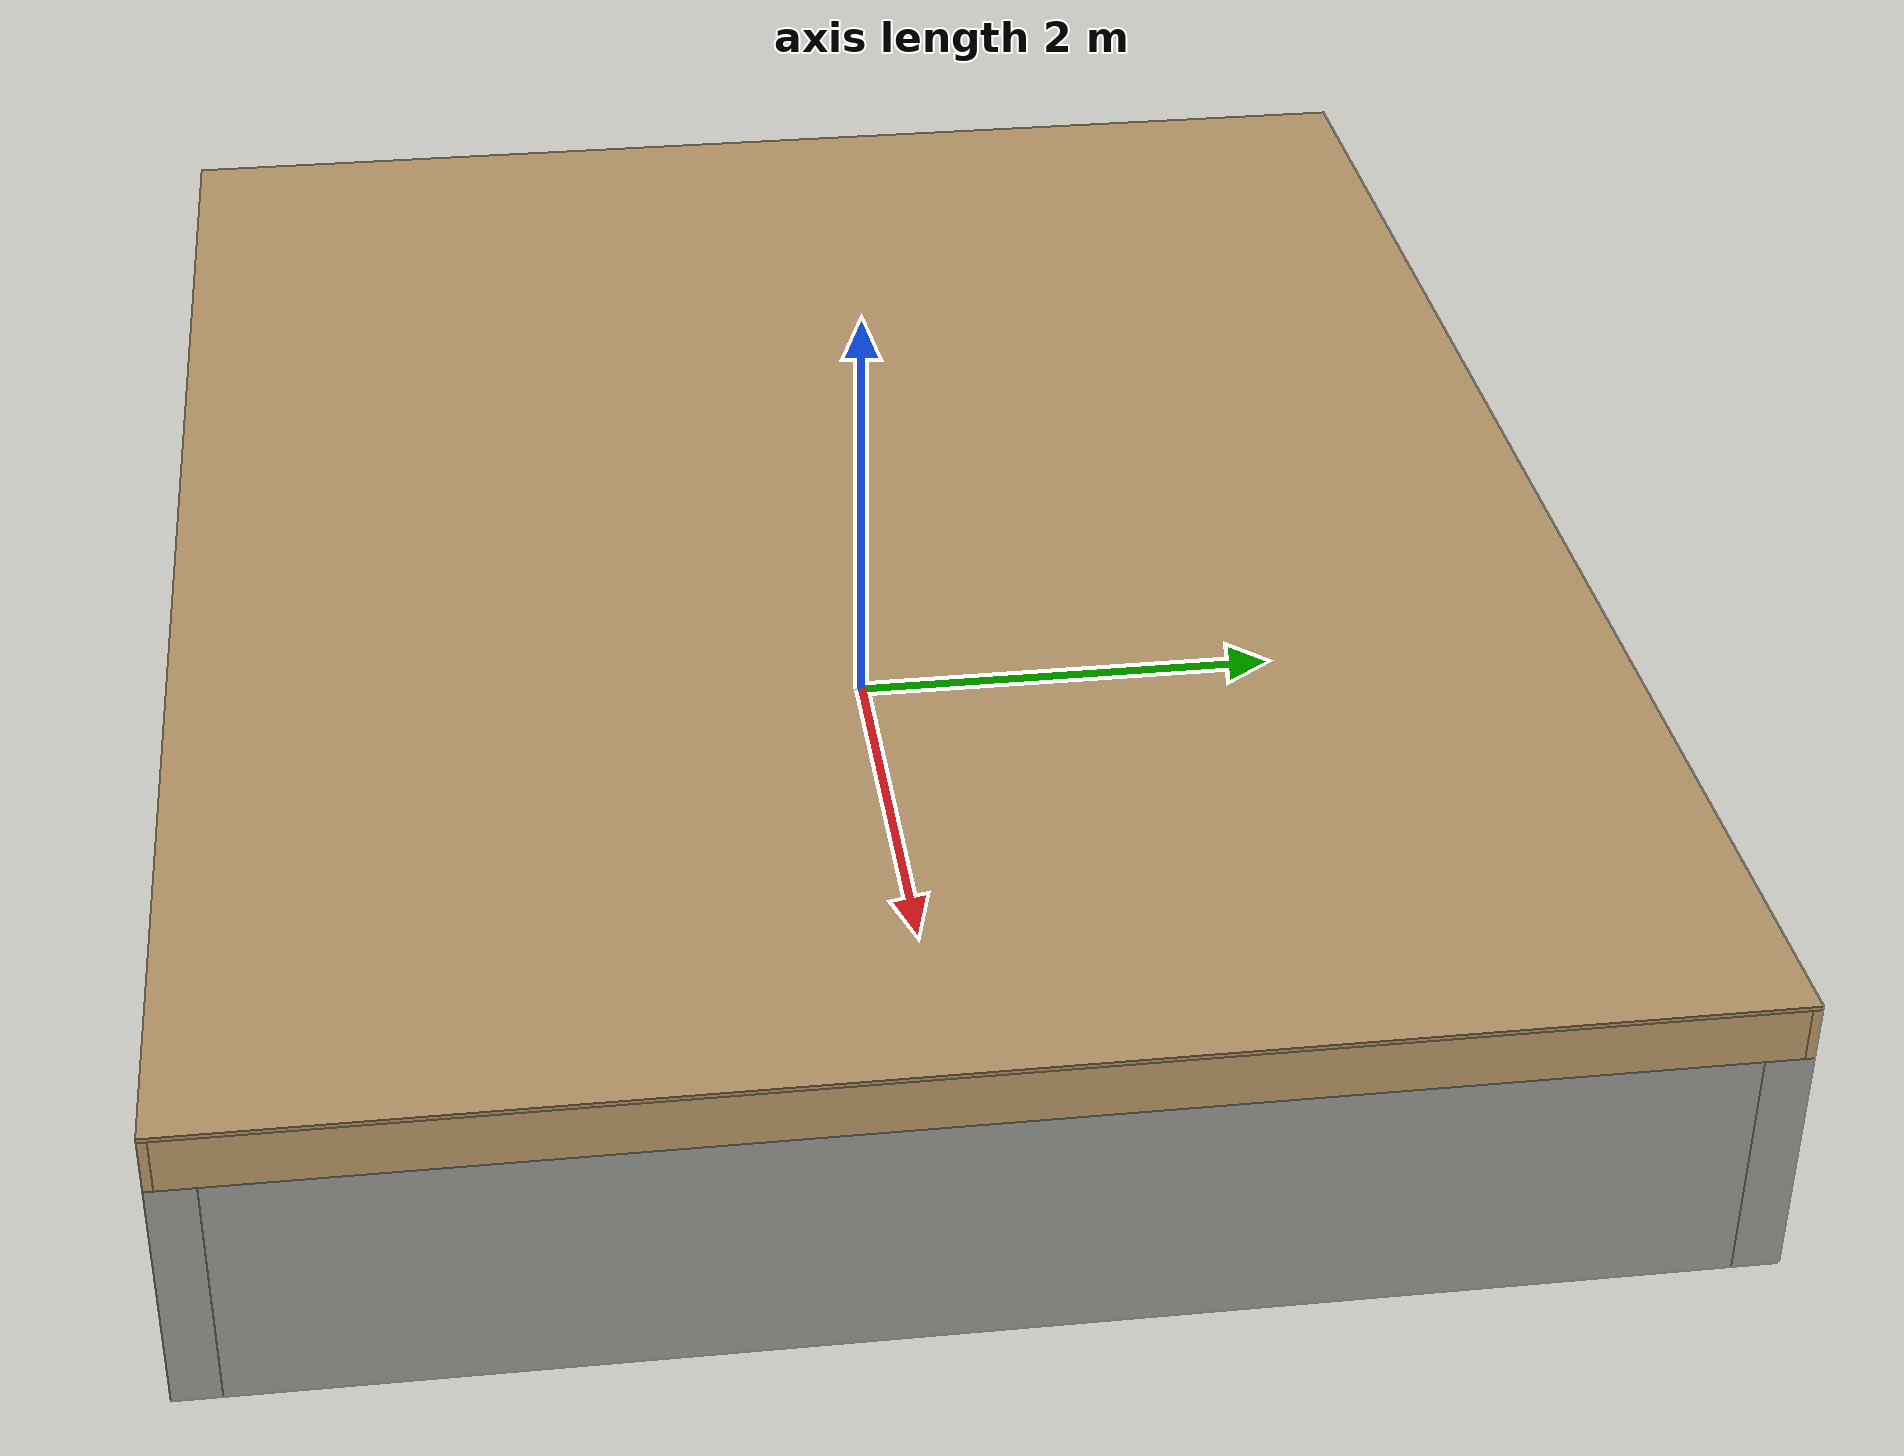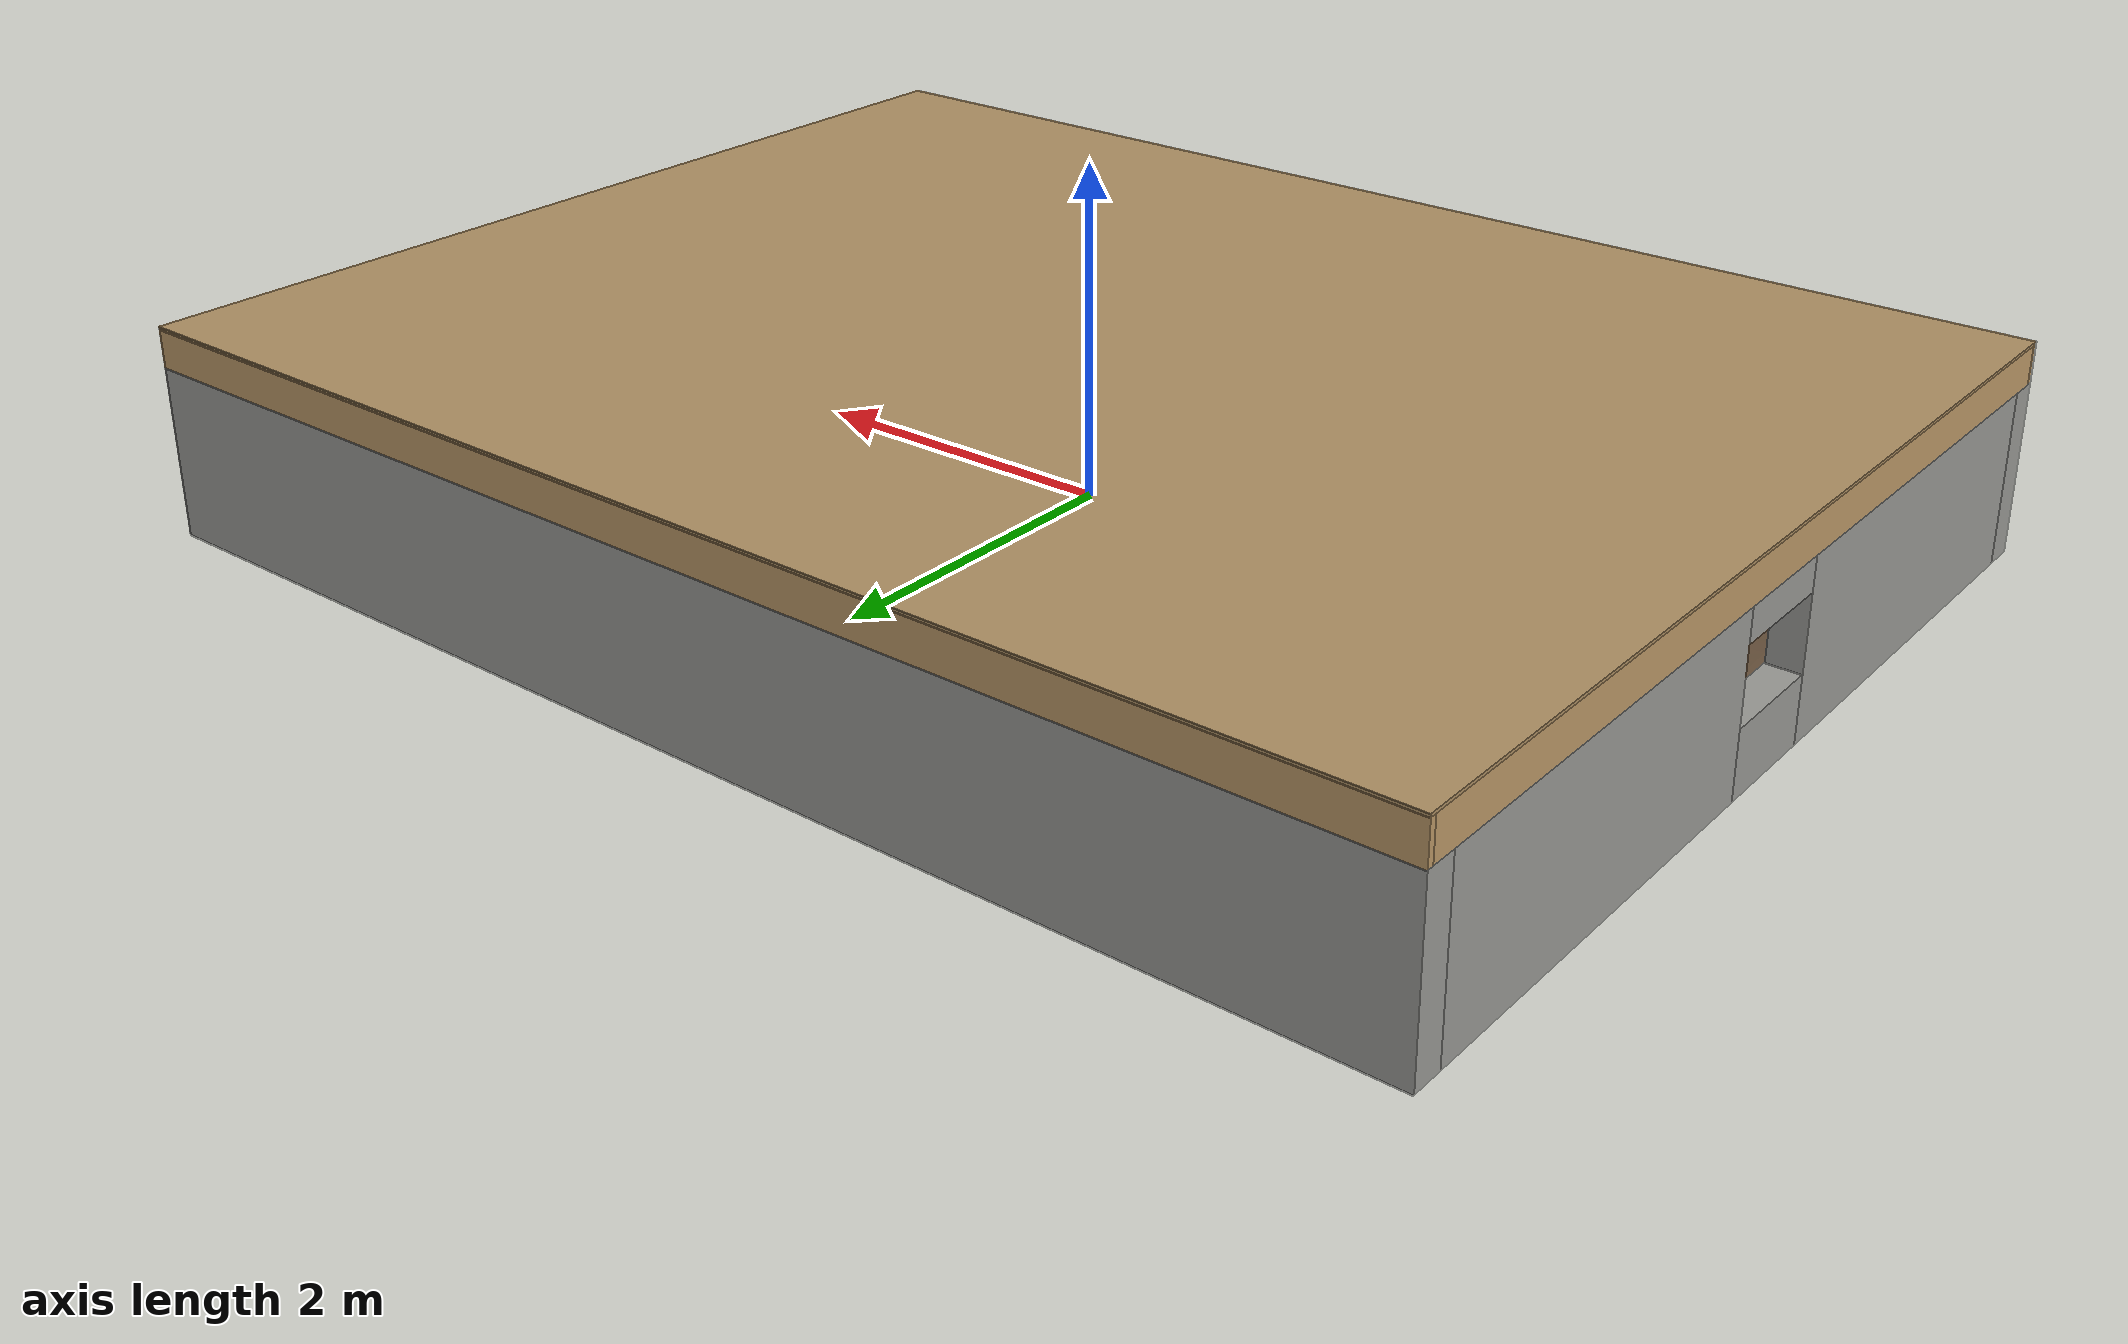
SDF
<?xml version='1.0' encoding='utf-8'?>
<sdf version="1.6">
  <!-- Generated by scripts/generate_crawlspace.py - edit that and re-run -->
  <world name="crawlspace">
    <physics type="ode">
      <max_step_size>0.001</max_step_size>
      <real_time_factor>1</real_time_factor>
      <real_time_update_rate>1000</real_time_update_rate>
    </physics>
    <gravity>0 0 -9.8</gravity>
    <scene>
      <ambient>0.3 0.3 0.3 1</ambient>
      <background>0.05 0.05 0.05 1</background>
      <shadows>false</shadows>
    </scene>
    <light name="work_light" type="point">
      <pose>0.5 -0.8 0.7 0 0 0</pose>
      <diffuse>1 0.85 0.65 1</diffuse>
      <specular>0.1 0.1 0.1 1</specular>
      <attenuation>
        <range>8</range>
        <constant>0.4</constant>
        <linear>0.1</linear>
        <quadratic>0.02</quadratic>
      </attenuation>
      <cast_shadows>false</cast_shadows>
    </light>
    <light name="access_daylight" type="point">
      <pose>-3.85 0 0.35 0 0 0</pose>
      <diffuse>0.75 0.8 0.9 1</diffuse>
      <specular>0.1 0.1 0.1 1</specular>
      <attenuation>
        <range>4</range>
        <constant>0.5</constant>
        <linear>0.3</linear>
        <quadratic>0.1</quadratic>
      </attenuation>
      <cast_shadows>false</cast_shadows>
    </light>
    <model name="terrain">
      <static>true</static>
      <link name="link">
        <visual name="dirt">
          <pose>0 0 0 0 0 0</pose>
          <geometry>
            <mesh>
              <uri>model://crawlspace_terrain/meshes/terrain.stl</uri>
            </mesh>
          </geometry>
          <material>
            <ambient>0.42 0.33 0.24 1</ambient>
            <diffuse>0.42 0.33 0.24 1</diffuse>
            <specular>0.05 0.05 0.05 1</specular>
          </material>
        </visual>
        <collision name="dirt">
          <pose>0 0 0 0 0 0</pose>
          <geometry>
            <mesh>
              <uri>model://crawlspace_terrain/meshes/terrain.stl</uri>
            </mesh>
          </geometry>
        </collision>
      </link>
    </model>
    <model name="damp_soil">
      <static>true</static>
      <link name="link">
        <visual name="damp">
          <pose>0 0 0 0 0 0</pose>
          <geometry>
            <mesh>
              <uri>model://crawlspace_terrain/meshes/damp_soil.stl</uri>
            </mesh>
          </geometry>
          <material>
            <ambient>0.26 0.19 0.13 1</ambient>
            <diffuse>0.26 0.19 0.13 1</diffuse>
            <specular>0.05 0.05 0.05 1</specular>
          </material>
        </visual>
      </link>
    </model>
    <model name="foundation_walls">
      <static>true</static>
      <link name="link">
        <visual name="north">
          <pose>0 3.1 0.225 0 0 0</pose>
          <geometry>
            <box>
              <size>8.4 0.2 1.05</size>
            </box>
          </geometry>
          <material>
            <ambient>0.62 0.62 0.6 1</ambient>
            <diffuse>0.62 0.62 0.6 1</diffuse>
            <specular>0.05 0.05 0.05 1</specular>
          </material>
        </visual>
        <collision name="north">
          <pose>0 3.1 0.225 0 0 0</pose>
          <geometry>
            <box>
              <size>8.4 0.2 1.05</size>
            </box>
          </geometry>
        </collision>
        <visual name="south">
          <pose>0 -3.1 0.225 0 0 0</pose>
          <geometry>
            <box>
              <size>8.4 0.2 1.05</size>
            </box>
          </geometry>
          <material>
            <ambient>0.62 0.62 0.6 1</ambient>
            <diffuse>0.62 0.62 0.6 1</diffuse>
            <specular>0.05 0.05 0.05 1</specular>
          </material>
        </visual>
        <collision name="south">
          <pose>0 -3.1 0.225 0 0 0</pose>
          <geometry>
            <box>
              <size>8.4 0.2 1.05</size>
            </box>
          </geometry>
        </collision>
        <visual name="east">
          <pose>4.1 0 0.225 0 0 0</pose>
          <geometry>
            <box>
              <size>0.2 6 1.05</size>
            </box>
          </geometry>
          <material>
            <ambient>0.62 0.62 0.6 1</ambient>
            <diffuse>0.62 0.62 0.6 1</diffuse>
            <specular>0.05 0.05 0.05 1</specular>
          </material>
        </visual>
        <collision name="east">
          <pose>4.1 0 0.225 0 0 0</pose>
          <geometry>
            <box>
              <size>0.2 6 1.05</size>
            </box>
          </geometry>
        </collision>
        <visual name="west_north">
          <pose>-4.1 1.675 0.225 0 0 0</pose>
          <geometry>
            <box>
              <size>0.2 2.65 1.05</size>
            </box>
          </geometry>
          <material>
            <ambient>0.62 0.62 0.6 1</ambient>
            <diffuse>0.62 0.62 0.6 1</diffuse>
            <specular>0.05 0.05 0.05 1</specular>
          </material>
        </visual>
        <collision name="west_north">
          <pose>-4.1 1.675 0.225 0 0 0</pose>
          <geometry>
            <box>
              <size>0.2 2.65 1.05</size>
            </box>
          </geometry>
        </collision>
        <visual name="west_south">
          <pose>-4.1 -1.675 0.225 0 0 0</pose>
          <geometry>
            <box>
              <size>0.2 2.65 1.05</size>
            </box>
          </geometry>
          <material>
            <ambient>0.62 0.62 0.6 1</ambient>
            <diffuse>0.62 0.62 0.6 1</diffuse>
            <specular>0.05 0.05 0.05 1</specular>
          </material>
        </visual>
        <collision name="west_south">
          <pose>-4.1 -1.675 0.225 0 0 0</pose>
          <geometry>
            <box>
              <size>0.2 2.65 1.05</size>
            </box>
          </geometry>
        </collision>
        <visual name="west_below_access">
          <pose>-4.1 0 -0.1 0 0 0</pose>
          <geometry>
            <box>
              <size>0.2 0.7 0.4</size>
            </box>
          </geometry>
          <material>
            <ambient>0.62 0.62 0.6 1</ambient>
            <diffuse>0.62 0.62 0.6 1</diffuse>
            <specular>0.05 0.05 0.05 1</specular>
          </material>
        </visual>
        <collision name="west_below_access">
          <pose>-4.1 0 -0.1 0 0 0</pose>
          <geometry>
            <box>
              <size>0.2 0.7 0.4</size>
            </box>
          </geometry>
        </collision>
        <visual name="west_above_access">
          <pose>-4.1 0 0.65 0 0 0</pose>
          <geometry>
            <box>
              <size>0.2 0.7 0.2</size>
            </box>
          </geometry>
          <material>
            <ambient>0.62 0.62 0.6 1</ambient>
            <diffuse>0.62 0.62 0.6 1</diffuse>
            <specular>0.05 0.05 0.05 1</specular>
          </material>
        </visual>
        <collision name="west_above_access">
          <pose>-4.1 0 0.65 0 0 0</pose>
          <geometry>
            <box>
              <size>0.2 0.7 0.2</size>
            </box>
          </geometry>
        </collision>
      </link>
    </model>
    <model name="floor_framing">
      <static>true</static>
      <link name="link">
        <visual name="girder">
          <pose>0 0 0.6325 0 0 0</pose>
          <geometry>
            <box>
              <size>8 0.12 0.235</size>
            </box>
          </geometry>
          <material>
            <ambient>0.76 0.62 0.42 1</ambient>
            <diffuse>0.76 0.62 0.42 1</diffuse>
            <specular>0.05 0.05 0.05 1</specular>
          </material>
        </visual>
        <collision name="girder">
          <pose>0 0 0.6325 0 0 0</pose>
          <geometry>
            <box>
              <size>8 0.12 0.235</size>
            </box>
          </geometry>
        </collision>
        <visual name="joist_00">
          <pose>-3.8 0 0.8675 0 0 0</pose>
          <geometry>
            <box>
              <size>0.04 6.32 0.235</size>
            </box>
          </geometry>
          <material>
            <ambient>0.76 0.62 0.42 1</ambient>
            <diffuse>0.76 0.62 0.42 1</diffuse>
            <specular>0.05 0.05 0.05 1</specular>
          </material>
        </visual>
        <collision name="joist_00">
          <pose>-3.8 0 0.8675 0 0 0</pose>
          <geometry>
            <box>
              <size>0.04 6.32 0.235</size>
            </box>
          </geometry>
        </collision>
        <visual name="joist_01">
          <pose>-3.4 0 0.8675 0 0 0</pose>
          <geometry>
            <box>
              <size>0.04 6.32 0.235</size>
            </box>
          </geometry>
          <material>
            <ambient>0.76 0.62 0.42 1</ambient>
            <diffuse>0.76 0.62 0.42 1</diffuse>
            <specular>0.05 0.05 0.05 1</specular>
          </material>
        </visual>
        <collision name="joist_01">
          <pose>-3.4 0 0.8675 0 0 0</pose>
          <geometry>
            <box>
              <size>0.04 6.32 0.235</size>
            </box>
          </geometry>
        </collision>
        <visual name="joist_02">
          <pose>-3 0 0.8675 0 0 0</pose>
          <geometry>
            <box>
              <size>0.04 6.32 0.235</size>
            </box>
          </geometry>
          <material>
            <ambient>0.76 0.62 0.42 1</ambient>
            <diffuse>0.76 0.62 0.42 1</diffuse>
            <specular>0.05 0.05 0.05 1</specular>
          </material>
        </visual>
        <collision name="joist_02">
          <pose>-3 0 0.8675 0 0 0</pose>
          <geometry>
            <box>
              <size>0.04 6.32 0.235</size>
            </box>
          </geometry>
        </collision>
        <visual name="joist_03">
          <pose>-2.6 0 0.8675 0 0 0</pose>
          <geometry>
            <box>
              <size>0.04 6.32 0.235</size>
            </box>
          </geometry>
          <material>
            <ambient>0.76 0.62 0.42 1</ambient>
            <diffuse>0.76 0.62 0.42 1</diffuse>
            <specular>0.05 0.05 0.05 1</specular>
          </material>
        </visual>
        <collision name="joist_03">
          <pose>-2.6 0 0.8675 0 0 0</pose>
          <geometry>
            <box>
              <size>0.04 6.32 0.235</size>
            </box>
          </geometry>
        </collision>
        <visual name="joist_04">
          <pose>-2.2 0 0.8675 0 0 0</pose>
          <geometry>
            <box>
              <size>0.04 6.32 0.235</size>
            </box>
          </geometry>
          <material>
            <ambient>0.76 0.62 0.42 1</ambient>
            <diffuse>0.76 0.62 0.42 1</diffuse>
            <specular>0.05 0.05 0.05 1</specular>
          </material>
        </visual>
        <collision name="joist_04">
          <pose>-2.2 0 0.8675 0 0 0</pose>
          <geometry>
            <box>
              <size>0.04 6.32 0.235</size>
            </box>
          </geometry>
        </collision>
        <visual name="joist_05">
          <pose>-1.8 0 0.8675 0 0 0</pose>
          <geometry>
            <box>
              <size>0.04 6.32 0.235</size>
            </box>
          </geometry>
          <material>
            <ambient>0.76 0.62 0.42 1</ambient>
            <diffuse>0.76 0.62 0.42 1</diffuse>
            <specular>0.05 0.05 0.05 1</specular>
          </material>
        </visual>
        <collision name="joist_05">
          <pose>-1.8 0 0.8675 0 0 0</pose>
          <geometry>
            <box>
              <size>0.04 6.32 0.235</size>
            </box>
          </geometry>
        </collision>
        <visual name="joist_06">
          <pose>-1.4 0 0.8675 0 0 0</pose>
          <geometry>
            <box>
              <size>0.04 6.32 0.235</size>
            </box>
          </geometry>
          <material>
            <ambient>0.76 0.62 0.42 1</ambient>
            <diffuse>0.76 0.62 0.42 1</diffuse>
            <specular>0.05 0.05 0.05 1</specular>
          </material>
        </visual>
        <collision name="joist_06">
          <pose>-1.4 0 0.8675 0 0 0</pose>
          <geometry>
            <box>
              <size>0.04 6.32 0.235</size>
            </box>
          </geometry>
        </collision>
        <visual name="joist_07">
          <pose>-1 0 0.8675 0 0 0</pose>
          <geometry>
            <box>
              <size>0.04 6.32 0.235</size>
            </box>
          </geometry>
          <material>
            <ambient>0.76 0.62 0.42 1</ambient>
            <diffuse>0.76 0.62 0.42 1</diffuse>
            <specular>0.05 0.05 0.05 1</specular>
          </material>
        </visual>
        <collision name="joist_07">
          <pose>-1 0 0.8675 0 0 0</pose>
          <geometry>
            <box>
              <size>0.04 6.32 0.235</size>
            </box>
          </geometry>
        </collision>
        <visual name="joist_08">
          <pose>-0.6 0 0.8675 0 0 0</pose>
          <geometry>
            <box>
              <size>0.04 6.32 0.235</size>
            </box>
          </geometry>
          <material>
            <ambient>0.76 0.62 0.42 1</ambient>
            <diffuse>0.76 0.62 0.42 1</diffuse>
            <specular>0.05 0.05 0.05 1</specular>
          </material>
        </visual>
        <collision name="joist_08">
          <pose>-0.6 0 0.8675 0 0 0</pose>
          <geometry>
            <box>
              <size>0.04 6.32 0.235</size>
            </box>
          </geometry>
        </collision>
        <visual name="joist_09">
          <pose>-0.2 0 0.8675 0 0 0</pose>
          <geometry>
            <box>
              <size>0.04 6.32 0.235</size>
            </box>
          </geometry>
          <material>
            <ambient>0.76 0.62 0.42 1</ambient>
            <diffuse>0.76 0.62 0.42 1</diffuse>
            <specular>0.05 0.05 0.05 1</specular>
          </material>
        </visual>
        <collision name="joist_09">
          <pose>-0.2 0 0.8675 0 0 0</pose>
          <geometry>
            <box>
              <size>0.04 6.32 0.235</size>
            </box>
          </geometry>
        </collision>
        <visual name="joist_10">
          <pose>0.2 0 0.8675 0 0 0</pose>
          <geometry>
            <box>
              <size>0.04 6.32 0.235</size>
            </box>
          </geometry>
          <material>
            <ambient>0.76 0.62 0.42 1</ambient>
            <diffuse>0.76 0.62 0.42 1</diffuse>
            <specular>0.05 0.05 0.05 1</specular>
          </material>
        </visual>
        <collision name="joist_10">
          <pose>0.2 0 0.8675 0 0 0</pose>
          <geometry>
            <box>
              <size>0.04 6.32 0.235</size>
            </box>
          </geometry>
        </collision>
        <visual name="joist_11">
          <pose>0.6 0 0.8675 0 0 0</pose>
          <geometry>
            <box>
              <size>0.04 6.32 0.235</size>
            </box>
          </geometry>
          <material>
            <ambient>0.76 0.62 0.42 1</ambient>
            <diffuse>0.76 0.62 0.42 1</diffuse>
            <specular>0.05 0.05 0.05 1</specular>
          </material>
        </visual>
        <collision name="joist_11">
          <pose>0.6 0 0.8675 0 0 0</pose>
          <geometry>
            <box>
              <size>0.04 6.32 0.235</size>
            </box>
          </geometry>
        </collision>
        <visual name="joist_12">
          <pose>1 0 0.8675 0 0 0</pose>
          <geometry>
            <box>
              <size>0.04 6.32 0.235</size>
            </box>
          </geometry>
          <material>
            <ambient>0.76 0.62 0.42 1</ambient>
            <diffuse>0.76 0.62 0.42 1</diffuse>
            <specular>0.05 0.05 0.05 1</specular>
          </material>
        </visual>
        <collision name="joist_12">
          <pose>1 0 0.8675 0 0 0</pose>
          <geometry>
            <box>
              <size>0.04 6.32 0.235</size>
            </box>
          </geometry>
        </collision>
        <visual name="joist_13">
          <pose>1.4 0 0.8675 0 0 0</pose>
          <geometry>
            <box>
              <size>0.04 6.32 0.235</size>
            </box>
          </geometry>
          <material>
            <ambient>0.76 0.62 0.42 1</ambient>
            <diffuse>0.76 0.62 0.42 1</diffuse>
            <specular>0.05 0.05 0.05 1</specular>
          </material>
        </visual>
        <collision name="joist_13">
          <pose>1.4 0 0.8675 0 0 0</pose>
          <geometry>
            <box>
              <size>0.04 6.32 0.235</size>
            </box>
          </geometry>
        </collision>
        <visual name="joist_14">
          <pose>1.8 0 0.8675 0 0 0</pose>
          <geometry>
            <box>
              <size>0.04 6.32 0.235</size>
            </box>
          </geometry>
          <material>
            <ambient>0.76 0.62 0.42 1</ambient>
            <diffuse>0.76 0.62 0.42 1</diffuse>
            <specular>0.05 0.05 0.05 1</specular>
          </material>
        </visual>
        <collision name="joist_14">
          <pose>1.8 0 0.8675 0 0 0</pose>
          <geometry>
            <box>
              <size>0.04 6.32 0.235</size>
            </box>
          </geometry>
        </collision>
        <visual name="joist_15">
          <pose>2.2 0 0.8675 0 0 0</pose>
          <geometry>
            <box>
              <size>0.04 6.32 0.235</size>
            </box>
          </geometry>
          <material>
            <ambient>0.76 0.62 0.42 1</ambient>
            <diffuse>0.76 0.62 0.42 1</diffuse>
            <specular>0.05 0.05 0.05 1</specular>
          </material>
        </visual>
        <collision name="joist_15">
          <pose>2.2 0 0.8675 0 0 0</pose>
          <geometry>
            <box>
              <size>0.04 6.32 0.235</size>
            </box>
          </geometry>
        </collision>
        <visual name="joist_16">
          <pose>2.6 0 0.8675 0 0 0</pose>
          <geometry>
            <box>
              <size>0.04 6.32 0.235</size>
            </box>
          </geometry>
          <material>
            <ambient>0.76 0.62 0.42 1</ambient>
            <diffuse>0.76 0.62 0.42 1</diffuse>
            <specular>0.05 0.05 0.05 1</specular>
          </material>
        </visual>
        <collision name="joist_16">
          <pose>2.6 0 0.8675 0 0 0</pose>
          <geometry>
            <box>
              <size>0.04 6.32 0.235</size>
            </box>
          </geometry>
        </collision>
        <visual name="joist_17">
          <pose>3 0 0.8675 0 0 0</pose>
          <geometry>
            <box>
              <size>0.04 6.32 0.235</size>
            </box>
          </geometry>
          <material>
            <ambient>0.76 0.62 0.42 1</ambient>
            <diffuse>0.76 0.62 0.42 1</diffuse>
            <specular>0.05 0.05 0.05 1</specular>
          </material>
        </visual>
        <collision name="joist_17">
          <pose>3 0 0.8675 0 0 0</pose>
          <geometry>
            <box>
              <size>0.04 6.32 0.235</size>
            </box>
          </geometry>
        </collision>
        <visual name="joist_18">
          <pose>3.4 0 0.8675 0 0 0</pose>
          <geometry>
            <box>
              <size>0.04 6.32 0.235</size>
            </box>
          </geometry>
          <material>
            <ambient>0.76 0.62 0.42 1</ambient>
            <diffuse>0.76 0.62 0.42 1</diffuse>
            <specular>0.05 0.05 0.05 1</specular>
          </material>
        </visual>
        <collision name="joist_18">
          <pose>3.4 0 0.8675 0 0 0</pose>
          <geometry>
            <box>
              <size>0.04 6.32 0.235</size>
            </box>
          </geometry>
        </collision>
        <visual name="joist_19">
          <pose>3.8 0 0.8675 0 0 0</pose>
          <geometry>
            <box>
              <size>0.04 6.32 0.235</size>
            </box>
          </geometry>
          <material>
            <ambient>0.76 0.62 0.42 1</ambient>
            <diffuse>0.76 0.62 0.42 1</diffuse>
            <specular>0.05 0.05 0.05 1</specular>
          </material>
        </visual>
        <collision name="joist_19">
          <pose>3.8 0 0.8675 0 0 0</pose>
          <geometry>
            <box>
              <size>0.04 6.32 0.235</size>
            </box>
          </geometry>
        </collision>
        <visual name="rim_north">
          <pose>0 3.18 0.8675 0 0 0</pose>
          <geometry>
            <box>
              <size>8.4 0.04 0.235</size>
            </box>
          </geometry>
          <material>
            <ambient>0.76 0.62 0.42 1</ambient>
            <diffuse>0.76 0.62 0.42 1</diffuse>
            <specular>0.05 0.05 0.05 1</specular>
          </material>
        </visual>
        <collision name="rim_north">
          <pose>0 3.18 0.8675 0 0 0</pose>
          <geometry>
            <box>
              <size>8.4 0.04 0.235</size>
            </box>
          </geometry>
        </collision>
        <visual name="rim_south">
          <pose>0 -3.18 0.8675 0 0 0</pose>
          <geometry>
            <box>
              <size>8.4 0.04 0.235</size>
            </box>
          </geometry>
          <material>
            <ambient>0.76 0.62 0.42 1</ambient>
            <diffuse>0.76 0.62 0.42 1</diffuse>
            <specular>0.05 0.05 0.05 1</specular>
          </material>
        </visual>
        <collision name="rim_south">
          <pose>0 -3.18 0.8675 0 0 0</pose>
          <geometry>
            <box>
              <size>8.4 0.04 0.235</size>
            </box>
          </geometry>
        </collision>
        <visual name="rim_east">
          <pose>4.18 0 0.8675 0 0 0</pose>
          <geometry>
            <box>
              <size>0.04 6.32 0.235</size>
            </box>
          </geometry>
          <material>
            <ambient>0.76 0.62 0.42 1</ambient>
            <diffuse>0.76 0.62 0.42 1</diffuse>
            <specular>0.05 0.05 0.05 1</specular>
          </material>
        </visual>
        <collision name="rim_east">
          <pose>4.18 0 0.8675 0 0 0</pose>
          <geometry>
            <box>
              <size>0.04 6.32 0.235</size>
            </box>
          </geometry>
        </collision>
        <visual name="rim_west">
          <pose>-4.18 0 0.8675 0 0 0</pose>
          <geometry>
            <box>
              <size>0.04 6.32 0.235</size>
            </box>
          </geometry>
          <material>
            <ambient>0.76 0.62 0.42 1</ambient>
            <diffuse>0.76 0.62 0.42 1</diffuse>
            <specular>0.05 0.05 0.05 1</specular>
          </material>
        </visual>
        <collision name="rim_west">
          <pose>-4.18 0 0.8675 0 0 0</pose>
          <geometry>
            <box>
              <size>0.04 6.32 0.235</size>
            </box>
          </geometry>
        </collision>
      </link>
    </model>
    <model name="subfloor">
      <static>true</static>
      <link name="link">
        <visual name="plywood">
          <pose>0 0 0.994 0 0 0</pose>
          <geometry>
            <box>
              <size>8.4 6.4 0.018</size>
            </box>
          </geometry>
          <material>
            <ambient>0.7 0.58 0.4 1</ambient>
            <diffuse>0.7 0.58 0.4 1</diffuse>
            <specular>0.05 0.05 0.05 1</specular>
          </material>
        </visual>
        <collision name="plywood">
          <pose>0 0 0.994 0 0 0</pose>
          <geometry>
            <box>
              <size>8.4 6.4 0.018</size>
            </box>
          </geometry>
        </collision>
      </link>
    </model>
    <model name="piers">
      <static>true</static>
      <link name="link">
        <visual name="footing_0">
          <pose>-2 0 -0.05 0 0 0</pose>
          <geometry>
            <box>
              <size>0.5 0.5 0.2</size>
            </box>
          </geometry>
          <material>
            <ambient>0.52 0.52 0.5 1</ambient>
            <diffuse>0.52 0.52 0.5 1</diffuse>
            <specular>0.05 0.05 0.05 1</specular>
          </material>
        </visual>
        <collision name="footing_0">
          <pose>-2 0 -0.05 0 0 0</pose>
          <geometry>
            <box>
              <size>0.5 0.5 0.2</size>
            </box>
          </geometry>
        </collision>
        <visual name="pier_0">
          <pose>-2 0 0.2825 0 0 0</pose>
          <geometry>
            <box>
              <size>0.4 0.4 0.465</size>
            </box>
          </geometry>
          <material>
            <ambient>0.62 0.62 0.6 1</ambient>
            <diffuse>0.62 0.62 0.6 1</diffuse>
            <specular>0.05 0.05 0.05 1</specular>
          </material>
        </visual>
        <collision name="pier_0">
          <pose>-2 0 0.2825 0 0 0</pose>
          <geometry>
            <box>
              <size>0.4 0.4 0.465</size>
            </box>
          </geometry>
        </collision>
        <visual name="footing_1">
          <pose>0 0 -0.05 0 0 0</pose>
          <geometry>
            <box>
              <size>0.5 0.5 0.2</size>
            </box>
          </geometry>
          <material>
            <ambient>0.52 0.52 0.5 1</ambient>
            <diffuse>0.52 0.52 0.5 1</diffuse>
            <specular>0.05 0.05 0.05 1</specular>
          </material>
        </visual>
        <collision name="footing_1">
          <pose>0 0 -0.05 0 0 0</pose>
          <geometry>
            <box>
              <size>0.5 0.5 0.2</size>
            </box>
          </geometry>
        </collision>
        <visual name="pier_1">
          <pose>0 0 0.2825 0 0 0</pose>
          <geometry>
            <box>
              <size>0.4 0.4 0.465</size>
            </box>
          </geometry>
          <material>
            <ambient>0.62 0.62 0.6 1</ambient>
            <diffuse>0.62 0.62 0.6 1</diffuse>
            <specular>0.05 0.05 0.05 1</specular>
          </material>
        </visual>
        <collision name="pier_1">
          <pose>0 0 0.2825 0 0 0</pose>
          <geometry>
            <box>
              <size>0.4 0.4 0.465</size>
            </box>
          </geometry>
        </collision>
        <visual name="footing_2">
          <pose>2 0 -0.05 0 0 0</pose>
          <geometry>
            <box>
              <size>0.5 0.5 0.2</size>
            </box>
          </geometry>
          <material>
            <ambient>0.52 0.52 0.5 1</ambient>
            <diffuse>0.52 0.52 0.5 1</diffuse>
            <specular>0.05 0.05 0.05 1</specular>
          </material>
        </visual>
        <collision name="footing_2">
          <pose>2 0 -0.05 0 0 0</pose>
          <geometry>
            <box>
              <size>0.5 0.5 0.2</size>
            </box>
          </geometry>
        </collision>
        <visual name="pier_2">
          <pose>2 0 0.2825 0 0 0</pose>
          <geometry>
            <box>
              <size>0.4 0.4 0.465</size>
            </box>
          </geometry>
          <material>
            <ambient>0.62 0.62 0.6 1</ambient>
            <diffuse>0.62 0.62 0.6 1</diffuse>
            <specular>0.05 0.05 0.05 1</specular>
          </material>
        </visual>
        <collision name="pier_2">
          <pose>2 0 0.2825 0 0 0</pose>
          <geometry>
            <box>
              <size>0.4 0.4 0.465</size>
            </box>
          </geometry>
        </collision>
      </link>
    </model>
    <model name="jack_posts">
      <static>true</static>
      <link name="link">
        <visual name="pad_0">
          <pose>1 2.2 0 0 0 0</pose>
          <geometry>
            <box>
              <size>0.3 0.3 0.1</size>
            </box>
          </geometry>
          <material>
            <ambient>0.52 0.52 0.5 1</ambient>
            <diffuse>0.52 0.52 0.5 1</diffuse>
            <specular>0.05 0.05 0.05 1</specular>
          </material>
        </visual>
        <collision name="pad_0">
          <pose>1 2.2 0 0 0 0</pose>
          <geometry>
            <box>
              <size>0.3 0.3 0.1</size>
            </box>
          </geometry>
        </collision>
        <visual name="post_0">
          <pose>1 2.2 0.4 0 0 0</pose>
          <geometry>
            <cylinder>
              <radius>0.025</radius>
              <length>0.7</length>
            </cylinder>
          </geometry>
          <material>
            <ambient>0.35 0.36 0.38 1</ambient>
            <diffuse>0.35 0.36 0.38 1</diffuse>
            <specular>0.05 0.05 0.05 1</specular>
          </material>
        </visual>
        <collision name="post_0">
          <pose>1 2.2 0.4 0 0 0</pose>
          <geometry>
            <cylinder>
              <radius>0.025</radius>
              <length>0.7</length>
            </cylinder>
          </geometry>
        </collision>
        <visual name="plate_0">
          <pose>1 2.2 0.746 0 0 0</pose>
          <geometry>
            <box>
              <size>0.15 0.15 0.008</size>
            </box>
          </geometry>
          <material>
            <ambient>0.35 0.36 0.38 1</ambient>
            <diffuse>0.35 0.36 0.38 1</diffuse>
            <specular>0.05 0.05 0.05 1</specular>
          </material>
        </visual>
        <collision name="plate_0">
          <pose>1 2.2 0.746 0 0 0</pose>
          <geometry>
            <box>
              <size>0.15 0.15 0.008</size>
            </box>
          </geometry>
        </collision>
        <visual name="pad_1">
          <pose>-1.4 -1.8 0 0 0 0</pose>
          <geometry>
            <box>
              <size>0.3 0.3 0.1</size>
            </box>
          </geometry>
          <material>
            <ambient>0.52 0.52 0.5 1</ambient>
            <diffuse>0.52 0.52 0.5 1</diffuse>
            <specular>0.05 0.05 0.05 1</specular>
          </material>
        </visual>
        <collision name="pad_1">
          <pose>-1.4 -1.8 0 0 0 0</pose>
          <geometry>
            <box>
              <size>0.3 0.3 0.1</size>
            </box>
          </geometry>
        </collision>
        <visual name="post_1">
          <pose>-1.4 -1.8 0.4 0 0 0</pose>
          <geometry>
            <cylinder>
              <radius>0.025</radius>
              <length>0.7</length>
            </cylinder>
          </geometry>
          <material>
            <ambient>0.35 0.36 0.38 1</ambient>
            <diffuse>0.35 0.36 0.38 1</diffuse>
            <specular>0.05 0.05 0.05 1</specular>
          </material>
        </visual>
        <collision name="post_1">
          <pose>-1.4 -1.8 0.4 0 0 0</pose>
          <geometry>
            <cylinder>
              <radius>0.025</radius>
              <length>0.7</length>
            </cylinder>
          </geometry>
        </collision>
        <visual name="plate_1">
          <pose>-1.4 -1.8 0.746 0 0 0</pose>
          <geometry>
            <box>
              <size>0.15 0.15 0.008</size>
            </box>
          </geometry>
          <material>
            <ambient>0.35 0.36 0.38 1</ambient>
            <diffuse>0.35 0.36 0.38 1</diffuse>
            <specular>0.05 0.05 0.05 1</specular>
          </material>
        </visual>
        <collision name="plate_1">
          <pose>-1.4 -1.8 0.746 0 0 0</pose>
          <geometry>
            <box>
              <size>0.15 0.15 0.008</size>
            </box>
          </geometry>
        </collision>
      </link>
    </model>
    <model name="plumbing">
      <static>true</static>
      <link name="link">
        <visual name="drain">
          <pose>-0.7 1.6 0.66 0 1.5708 0</pose>
          <geometry>
            <cylinder>
              <radius>0.05</radius>
              <length>6.4</length>
            </cylinder>
          </geometry>
          <material>
            <ambient>0.92 0.92 0.9 1</ambient>
            <diffuse>0.92 0.92 0.9 1</diffuse>
            <specular>0.05 0.05 0.05 1</specular>
          </material>
        </visual>
        <collision name="drain">
          <pose>-0.7 1.6 0.66 0 1.5708 0</pose>
          <geometry>
            <cylinder>
              <radius>0.05</radius>
              <length>6.4</length>
            </cylinder>
          </geometry>
        </collision>
        <visual name="drain_riser">
          <pose>2.5 1.6 0.8225 0 0 0</pose>
          <geometry>
            <cylinder>
              <radius>0.05</radius>
              <length>0.325</length>
            </cylinder>
          </geometry>
          <material>
            <ambient>0.92 0.92 0.9 1</ambient>
            <diffuse>0.92 0.92 0.9 1</diffuse>
            <specular>0.05 0.05 0.05 1</specular>
          </material>
        </visual>
        <collision name="drain_riser">
          <pose>2.5 1.6 0.8225 0 0 0</pose>
          <geometry>
            <cylinder>
              <radius>0.05</radius>
              <length>0.325</length>
            </cylinder>
          </geometry>
        </collision>
        <visual name="supply_0">
          <pose>-0.4 -1 0.72 0 1.5708 0</pose>
          <geometry>
            <cylinder>
              <radius>0.011</radius>
              <length>7</length>
            </cylinder>
          </geometry>
          <material>
            <ambient>0.72 0.45 0.2 1</ambient>
            <diffuse>0.72 0.45 0.2 1</diffuse>
            <specular>0.05 0.05 0.05 1</specular>
          </material>
        </visual>
        <collision name="supply_0">
          <pose>-0.4 -1 0.72 0 1.5708 0</pose>
          <geometry>
            <cylinder>
              <radius>0.011</radius>
              <length>7</length>
            </cylinder>
          </geometry>
        </collision>
        <visual name="supply_1">
          <pose>-0.4 -1.08 0.72 0 1.5708 0</pose>
          <geometry>
            <cylinder>
              <radius>0.011</radius>
              <length>7</length>
            </cylinder>
          </geometry>
          <material>
            <ambient>0.72 0.45 0.2 1</ambient>
            <diffuse>0.72 0.45 0.2 1</diffuse>
            <specular>0.05 0.05 0.05 1</specular>
          </material>
        </visual>
        <collision name="supply_1">
          <pose>-0.4 -1.08 0.72 0 1.5708 0</pose>
          <geometry>
            <cylinder>
              <radius>0.011</radius>
              <length>7</length>
            </cylinder>
          </geometry>
        </collision>
      </link>
    </model>
    <model name="hvac">
      <static>true</static>
      <link name="link">
        <visual name="flex_duct">
          <pose>2.4 -1.725 0.58 1.5708 0 0</pose>
          <geometry>
            <cylinder>
              <radius>0.15</radius>
              <length>2.55</length>
            </cylinder>
          </geometry>
          <material>
            <ambient>0.75 0.76 0.78 1</ambient>
            <diffuse>0.75 0.76 0.78 1</diffuse>
            <specular>0.05 0.05 0.05 1</specular>
          </material>
        </visual>
        <collision name="flex_duct">
          <pose>2.4 -1.725 0.58 1.5708 0 0</pose>
          <geometry>
            <cylinder>
              <radius>0.15</radius>
              <length>2.55</length>
            </cylinder>
          </geometry>
        </collision>
        <visual name="register_boot">
          <pose>2.4 -0.3 0.75 0 0 0</pose>
          <geometry>
            <box>
              <size>0.3 0.3 0.3</size>
            </box>
          </geometry>
          <material>
            <ambient>0.75 0.76 0.78 1</ambient>
            <diffuse>0.75 0.76 0.78 1</diffuse>
            <specular>0.05 0.05 0.05 1</specular>
          </material>
        </visual>
        <collision name="register_boot">
          <pose>2.4 -0.3 0.75 0 0 0</pose>
          <geometry>
            <box>
              <size>0.3 0.3 0.3</size>
            </box>
          </geometry>
        </collision>
      </link>
    </model>
    <model name="rocks">
      <static>true</static>
      <link name="link">
        <visual name="rock_00">
          <pose>-2.0224 2.4964 0.017 -0.1744 0.0851 1.4424</pose>
          <geometry>
            <box>
              <size>0.0436 0.0292 0.0194</size>
            </box>
          </geometry>
          <material>
            <ambient>0.5398 0.5159 0.4799 1</ambient>
            <diffuse>0.5398 0.5159 0.4799 1</diffuse>
            <specular>0.05 0.05 0.05 1</specular>
          </material>
        </visual>
        <collision name="rock_00">
          <pose>-2.0224 2.4964 0.017 -0.1744 0.0851 1.4424</pose>
          <geometry>
            <box>
              <size>0.0436 0.0292 0.0194</size>
            </box>
          </geometry>
        </collision>
        <visual name="rock_01">
          <pose>-1.7259 -0.4986 0.0122 -0.2621 0.0721 1.185</pose>
          <geometry>
            <box>
              <size>0.0864 0.0716 0.0469</size>
            </box>
          </geometry>
          <material>
            <ambient>0.5385 0.5146 0.4787 1</ambient>
            <diffuse>0.5385 0.5146 0.4787 1</diffuse>
            <specular>0.05 0.05 0.05 1</specular>
          </material>
        </visual>
        <collision name="rock_01">
          <pose>-1.7259 -0.4986 0.0122 -0.2621 0.0721 1.185</pose>
          <geometry>
            <box>
              <size>0.0864 0.0716 0.0469</size>
            </box>
          </geometry>
        </collision>
        <visual name="rock_02">
          <pose>1.1902 -0.8724 -0.0095 -0.2147 -0.2614 2.9721</pose>
          <geometry>
            <box>
              <size>0.0783 0.0854 0.0596</size>
            </box>
          </geometry>
          <material>
            <ambient>0.4647 0.444 0.413 1</ambient>
            <diffuse>0.4647 0.444 0.413 1</diffuse>
            <specular>0.05 0.05 0.05 1</specular>
          </material>
        </visual>
        <collision name="rock_02">
          <pose>1.1902 -0.8724 -0.0095 -0.2147 -0.2614 2.9721</pose>
          <geometry>
            <box>
              <size>0.0783 0.0854 0.0596</size>
            </box>
          </geometry>
        </collision>
        <visual name="rock_03">
          <pose>-0.0839 -1.6532 0.0164 -0.086 0.2268 0.424</pose>
          <geometry>
            <box>
              <size>0.1008 0.1094 0.0724</size>
            </box>
          </geometry>
          <material>
            <ambient>0.4114 0.3931 0.3657 1</ambient>
            <diffuse>0.4114 0.3931 0.3657 1</diffuse>
            <specular>0.05 0.05 0.05 1</specular>
          </material>
        </visual>
        <collision name="rock_03">
          <pose>-0.0839 -1.6532 0.0164 -0.086 0.2268 0.424</pose>
          <geometry>
            <box>
              <size>0.1008 0.1094 0.0724</size>
            </box>
          </geometry>
        </collision>
        <visual name="rock_04">
          <pose>-2.2374 -1.8891 0.0941 0.1208 -0.168 0.7662</pose>
          <geometry>
            <box>
              <size>0.0674 0.0498 0.051</size>
            </box>
          </geometry>
          <material>
            <ambient>0.4513 0.4313 0.4012 1</ambient>
            <diffuse>0.4513 0.4313 0.4012 1</diffuse>
            <specular>0.05 0.05 0.05 1</specular>
          </material>
        </visual>
        <collision name="rock_04">
          <pose>-2.2374 -1.8891 0.0941 0.1208 -0.168 0.7662</pose>
          <geometry>
            <box>
              <size>0.0674 0.0498 0.051</size>
            </box>
          </geometry>
        </collision>
        <visual name="rock_05">
          <pose>-3.6118 -0.8466 -0.0006 -0.1948 -0.0622 0.5221</pose>
          <geometry>
            <box>
              <size>0.0464 0.0451 0.0357</size>
            </box>
          </geometry>
          <material>
            <ambient>0.5205 0.4973 0.4626 1</ambient>
            <diffuse>0.5205 0.4973 0.4626 1</diffuse>
            <specular>0.05 0.05 0.05 1</specular>
          </material>
        </visual>
        <collision name="rock_05">
          <pose>-3.6118 -0.8466 -0.0006 -0.1948 -0.0622 0.5221</pose>
          <geometry>
            <box>
              <size>0.0464 0.0451 0.0357</size>
            </box>
          </geometry>
        </collision>
        <visual name="rock_06">
          <pose>1.2075 2.5642 0.0568 -0.0949 -0.1979 1.3685</pose>
          <geometry>
            <box>
              <size>0.0512 0.0388 0.0179</size>
            </box>
          </geometry>
          <material>
            <ambient>0.4976 0.4755 0.4423 1</ambient>
            <diffuse>0.4976 0.4755 0.4423 1</diffuse>
            <specular>0.05 0.05 0.05 1</specular>
          </material>
        </visual>
        <collision name="rock_06">
          <pose>1.2075 2.5642 0.0568 -0.0949 -0.1979 1.3685</pose>
          <geometry>
            <box>
              <size>0.0512 0.0388 0.0179</size>
            </box>
          </geometry>
        </collision>
        <visual name="rock_07">
          <pose>-3.0691 -2.1248 0.0328 0.288 -0.2622 0.0532</pose>
          <geometry>
            <box>
              <size>0.0609 0.0787 0.04</size>
            </box>
          </geometry>
          <material>
            <ambient>0.4875 0.4658 0.4333 1</ambient>
            <diffuse>0.4875 0.4658 0.4333 1</diffuse>
            <specular>0.05 0.05 0.05 1</specular>
          </material>
        </visual>
        <collision name="rock_07">
          <pose>-3.0691 -2.1248 0.0328 0.288 -0.2622 0.0532</pose>
          <geometry>
            <box>
              <size>0.0609 0.0787 0.04</size>
            </box>
          </geometry>
        </collision>
        <visual name="rock_08">
          <pose>-2.6611 -0.6138 0.0182 0.2014 -0.174 2.7495</pose>
          <geometry>
            <box>
              <size>0.0804 0.0639 0.0551</size>
            </box>
          </geometry>
          <material>
            <ambient>0.3605 0.3445 0.3205 1</ambient>
            <diffuse>0.3605 0.3445 0.3205 1</diffuse>
            <specular>0.05 0.05 0.05 1</specular>
          </material>
        </visual>
        <collision name="rock_08">
          <pose>-2.6611 -0.6138 0.0182 0.2014 -0.174 2.7495</pose>
          <geometry>
            <box>
              <size>0.0804 0.0639 0.0551</size>
            </box>
          </geometry>
        </collision>
        <visual name="rock_09">
          <pose>-3.4549 2.5119 0.0041 -0.0351 -0.25 1.9019</pose>
          <geometry>
            <box>
              <size>0.1076 0.0871 0.0392</size>
            </box>
          </geometry>
          <material>
            <ambient>0.5346 0.5108 0.4752 1</ambient>
            <diffuse>0.5346 0.5108 0.4752 1</diffuse>
            <specular>0.05 0.05 0.05 1</specular>
          </material>
        </visual>
        <collision name="rock_09">
          <pose>-3.4549 2.5119 0.0041 -0.0351 -0.25 1.9019</pose>
          <geometry>
            <box>
              <size>0.1076 0.0871 0.0392</size>
            </box>
          </geometry>
        </collision>
        <visual name="rock_10">
          <pose>-0.4478 1.2178 0.0209 -0.1815 -0.0323 0.3399</pose>
          <geometry>
            <box>
              <size>0.0787 0.075 0.0436</size>
            </box>
          </geometry>
          <material>
            <ambient>0.4006 0.3828 0.3561 1</ambient>
            <diffuse>0.4006 0.3828 0.3561 1</diffuse>
            <specular>0.05 0.05 0.05 1</specular>
          </material>
        </visual>
        <collision name="rock_10">
          <pose>-0.4478 1.2178 0.0209 -0.1815 -0.0323 0.3399</pose>
          <geometry>
            <box>
              <size>0.0787 0.075 0.0436</size>
            </box>
          </geometry>
        </collision>
        <visual name="rock_11">
          <pose>1.666 1.1249 0.0021 0.2807 0.1534 1.5789</pose>
          <geometry>
            <box>
              <size>0.052 0.0669 0.0417</size>
            </box>
          </geometry>
          <material>
            <ambient>0.3768 0.3601 0.3349 1</ambient>
            <diffuse>0.3768 0.3601 0.3349 1</diffuse>
            <specular>0.05 0.05 0.05 1</specular>
          </material>
        </visual>
        <collision name="rock_11">
          <pose>1.666 1.1249 0.0021 0.2807 0.1534 1.5789</pose>
          <geometry>
            <box>
              <size>0.052 0.0669 0.0417</size>
            </box>
          </geometry>
        </collision>
        <visual name="rock_12">
          <pose>1.5183 -1.6163 0.0058 0.0679 0.2453 2.3351</pose>
          <geometry>
            <box>
              <size>0.0468 0.0528 0.0303</size>
            </box>
          </geometry>
          <material>
            <ambient>0.3612 0.3451 0.3211 1</ambient>
            <diffuse>0.3612 0.3451 0.3211 1</diffuse>
            <specular>0.05 0.05 0.05 1</specular>
          </material>
        </visual>
        <collision name="rock_12">
          <pose>1.5183 -1.6163 0.0058 0.0679 0.2453 2.3351</pose>
          <geometry>
            <box>
              <size>0.0468 0.0528 0.0303</size>
            </box>
          </geometry>
        </collision>
        <visual name="rock_13">
          <pose>3.1641 2.6013 0.007 0.2649 0.2103 1.6219</pose>
          <geometry>
            <box>
              <size>0.0401 0.047 0.0361</size>
            </box>
          </geometry>
          <material>
            <ambient>0.4265 0.4075 0.3791 1</ambient>
            <diffuse>0.4265 0.4075 0.3791 1</diffuse>
            <specular>0.05 0.05 0.05 1</specular>
          </material>
        </visual>
        <collision name="rock_13">
          <pose>3.1641 2.6013 0.007 0.2649 0.2103 1.6219</pose>
          <geometry>
            <box>
              <size>0.0401 0.047 0.0361</size>
            </box>
          </geometry>
        </collision>
        <visual name="rock_14">
          <pose>3.3935 1.8741 0.0055 0.2616 0.1368 2.579</pose>
          <geometry>
            <box>
              <size>0.0453 0.0554 0.0382</size>
            </box>
          </geometry>
          <material>
            <ambient>0.4832 0.4617 0.4295 1</ambient>
            <diffuse>0.4832 0.4617 0.4295 1</diffuse>
            <specular>0.05 0.05 0.05 1</specular>
          </material>
        </visual>
        <collision name="rock_14">
          <pose>3.3935 1.8741 0.0055 0.2616 0.1368 2.579</pose>
          <geometry>
            <box>
              <size>0.0453 0.0554 0.0382</size>
            </box>
          </geometry>
        </collision>
        <visual name="rock_15">
          <pose>0.7765 -0.7442 -0.0031 -0.2588 0.1399 0.851</pose>
          <geometry>
            <box>
              <size>0.0596 0.061 0.0441</size>
            </box>
          </geometry>
          <material>
            <ambient>0.4084 0.3902 0.363 1</ambient>
            <diffuse>0.4084 0.3902 0.363 1</diffuse>
            <specular>0.05 0.05 0.05 1</specular>
          </material>
        </visual>
        <collision name="rock_15">
          <pose>0.7765 -0.7442 -0.0031 -0.2588 0.1399 0.851</pose>
          <geometry>
            <box>
              <size>0.0596 0.061 0.0441</size>
            </box>
          </geometry>
        </collision>
        <visual name="rock_16">
          <pose>-0.594 -2.068 0.002 -0.1336 0.233 1.2937</pose>
          <geometry>
            <box>
              <size>0.0761 0.077 0.0635</size>
            </box>
          </geometry>
          <material>
            <ambient>0.4508 0.4307 0.4007 1</ambient>
            <diffuse>0.4508 0.4307 0.4007 1</diffuse>
            <specular>0.05 0.05 0.05 1</specular>
          </material>
        </visual>
        <collision name="rock_16">
          <pose>-0.594 -2.068 0.002 -0.1336 0.233 1.2937</pose>
          <geometry>
            <box>
              <size>0.0761 0.077 0.0635</size>
            </box>
          </geometry>
        </collision>
        <visual name="rock_17">
          <pose>-1.0259 2.5134 0.0158 0.1978 -0.0792 2.4528</pose>
          <geometry>
            <box>
              <size>0.098 0.0725 0.0619</size>
            </box>
          </geometry>
          <material>
            <ambient>0.4674 0.4466 0.4155 1</ambient>
            <diffuse>0.4674 0.4466 0.4155 1</diffuse>
            <specular>0.05 0.05 0.05 1</specular>
          </material>
        </visual>
        <collision name="rock_17">
          <pose>-1.0259 2.5134 0.0158 0.1978 -0.0792 2.4528</pose>
          <geometry>
            <box>
              <size>0.098 0.0725 0.0619</size>
            </box>
          </geometry>
        </collision>
        <visual name="rock_18">
          <pose>2.1714 -0.6051 0.0061 -0.2179 0.0662 2.1521</pose>
          <geometry>
            <box>
              <size>0.0886 0.0983 0.0582</size>
            </box>
          </geometry>
          <material>
            <ambient>0.5015 0.4792 0.4458 1</ambient>
            <diffuse>0.5015 0.4792 0.4458 1</diffuse>
            <specular>0.05 0.05 0.05 1</specular>
          </material>
        </visual>
        <collision name="rock_18">
          <pose>2.1714 -0.6051 0.0061 -0.2179 0.0662 2.1521</pose>
          <geometry>
            <box>
              <size>0.0886 0.0983 0.0582</size>
            </box>
          </geometry>
        </collision>
        <visual name="rock_19">
          <pose>2.7011 0.8246 0.0073 -0.0803 0.1971 2.5598</pose>
          <geometry>
            <box>
              <size>0.0379 0.0656 0.039</size>
            </box>
          </geometry>
          <material>
            <ambient>0.4777 0.4564 0.4246 1</ambient>
            <diffuse>0.4777 0.4564 0.4246 1</diffuse>
            <specular>0.05 0.05 0.05 1</specular>
          </material>
        </visual>
        <collision name="rock_19">
          <pose>2.7011 0.8246 0.0073 -0.0803 0.1971 2.5598</pose>
          <geometry>
            <box>
              <size>0.0379 0.0656 0.039</size>
            </box>
          </geometry>
        </collision>
        <visual name="rock_20">
          <pose>1.6629 0.5386 0.0136 -0.2316 0.1328 1.0934</pose>
          <geometry>
            <box>
              <size>0.046 0.0479 0.0278</size>
            </box>
          </geometry>
          <material>
            <ambient>0.4536 0.4334 0.4032 1</ambient>
            <diffuse>0.4536 0.4334 0.4032 1</diffuse>
            <specular>0.05 0.05 0.05 1</specular>
          </material>
        </visual>
        <collision name="rock_20">
          <pose>1.6629 0.5386 0.0136 -0.2316 0.1328 1.0934</pose>
          <geometry>
            <box>
              <size>0.046 0.0479 0.0278</size>
            </box>
          </geometry>
        </collision>
        <visual name="rock_21">
          <pose>-2.5179 -1.3235 0.033 -0.1241 -0.194 2.3543</pose>
          <geometry>
            <box>
              <size>0.0549 0.0669 0.0252</size>
            </box>
          </geometry>
          <material>
            <ambient>0.4001 0.3823 0.3556 1</ambient>
            <diffuse>0.4001 0.3823 0.3556 1</diffuse>
            <specular>0.05 0.05 0.05 1</specular>
          </material>
        </visual>
        <collision name="rock_21">
          <pose>-2.5179 -1.3235 0.033 -0.1241 -0.194 2.3543</pose>
          <geometry>
            <box>
              <size>0.0549 0.0669 0.0252</size>
            </box>
          </geometry>
        </collision>
        <visual name="rock_22">
          <pose>-2.8933 -2.4253 0.0108 0.2291 0.1417 1.5045</pose>
          <geometry>
            <box>
              <size>0.0787 0.0824 0.043</size>
            </box>
          </geometry>
          <material>
            <ambient>0.4188 0.4002 0.3723 1</ambient>
            <diffuse>0.4188 0.4002 0.3723 1</diffuse>
            <specular>0.05 0.05 0.05 1</specular>
          </material>
        </visual>
        <collision name="rock_22">
          <pose>-2.8933 -2.4253 0.0108 0.2291 0.1417 1.5045</pose>
          <geometry>
            <box>
              <size>0.0787 0.0824 0.043</size>
            </box>
          </geometry>
        </collision>
        <visual name="rock_23">
          <pose>0.465 2.3547 0.0514 -0.1986 0.1572 0.1912</pose>
          <geometry>
            <box>
              <size>0.1256 0.0778 0.053</size>
            </box>
          </geometry>
          <material>
            <ambient>0.4334 0.4141 0.3853 1</ambient>
            <diffuse>0.4334 0.4141 0.3853 1</diffuse>
            <specular>0.05 0.05 0.05 1</specular>
          </material>
        </visual>
        <collision name="rock_23">
          <pose>0.465 2.3547 0.0514 -0.1986 0.1572 0.1912</pose>
          <geometry>
            <box>
              <size>0.1256 0.0778 0.053</size>
            </box>
          </geometry>
        </collision>
        <visual name="rock_24">
          <pose>2.8671 0.462 0.0126 0.2536 0.1153 3.0893</pose>
          <geometry>
            <box>
              <size>0.0692 0.0921 0.0461</size>
            </box>
          </geometry>
          <material>
            <ambient>0.5214 0.4982 0.4634 1</ambient>
            <diffuse>0.5214 0.4982 0.4634 1</diffuse>
            <specular>0.05 0.05 0.05 1</specular>
          </material>
        </visual>
        <collision name="rock_24">
          <pose>2.8671 0.462 0.0126 0.2536 0.1153 3.0893</pose>
          <geometry>
            <box>
              <size>0.0692 0.0921 0.0461</size>
            </box>
          </geometry>
        </collision>
        <visual name="rock_25">
          <pose>-0.0767 -0.7206 0.0041 -0.2233 0.2027 1.5706</pose>
          <geometry>
            <box>
              <size>0.0906 0.0789 0.0599</size>
            </box>
          </geometry>
          <material>
            <ambient>0.4457 0.4259 0.3961 1</ambient>
            <diffuse>0.4457 0.4259 0.3961 1</diffuse>
            <specular>0.05 0.05 0.05 1</specular>
          </material>
        </visual>
        <collision name="rock_25">
          <pose>-0.0767 -0.7206 0.0041 -0.2233 0.2027 1.5706</pose>
          <geometry>
            <box>
              <size>0.0906 0.0789 0.0599</size>
            </box>
          </geometry>
        </collision>
        <visual name="rock_26">
          <pose>3.4896 0.1818 0.008 0.1949 0.0885 0.3904</pose>
          <geometry>
            <box>
              <size>0.0835 0.0794 0.0584</size>
            </box>
          </geometry>
          <material>
            <ambient>0.498 0.4759 0.4427 1</ambient>
            <diffuse>0.498 0.4759 0.4427 1</diffuse>
            <specular>0.05 0.05 0.05 1</specular>
          </material>
        </visual>
        <collision name="rock_26">
          <pose>3.4896 0.1818 0.008 0.1949 0.0885 0.3904</pose>
          <geometry>
            <box>
              <size>0.0835 0.0794 0.0584</size>
            </box>
          </geometry>
        </collision>
        <visual name="rock_27">
          <pose>-0.7838 -2.5113 -0.0074 -0.2141 0.113 0.2504</pose>
          <geometry>
            <box>
              <size>0.0709 0.0509 0.0381</size>
            </box>
          </geometry>
          <material>
            <ambient>0.4719 0.4509 0.4194 1</ambient>
            <diffuse>0.4719 0.4509 0.4194 1</diffuse>
            <specular>0.05 0.05 0.05 1</specular>
          </material>
        </visual>
        <collision name="rock_27">
          <pose>-0.7838 -2.5113 -0.0074 -0.2141 0.113 0.2504</pose>
          <geometry>
            <box>
              <size>0.0709 0.0509 0.0381</size>
            </box>
          </geometry>
        </collision>
        <visual name="rock_28">
          <pose>-2.3336 0.4316 -0.0328 -0.2352 0.2994 0.1244</pose>
          <geometry>
            <box>
              <size>0.0498 0.0372 0.0254</size>
            </box>
          </geometry>
          <material>
            <ambient>0.5337 0.51 0.4744 1</ambient>
            <diffuse>0.5337 0.51 0.4744 1</diffuse>
            <specular>0.05 0.05 0.05 1</specular>
          </material>
        </visual>
        <collision name="rock_28">
          <pose>-2.3336 0.4316 -0.0328 -0.2352 0.2994 0.1244</pose>
          <geometry>
            <box>
              <size>0.0498 0.0372 0.0254</size>
            </box>
          </geometry>
        </collision>
        <visual name="rock_29">
          <pose>0.7492 0.842 0.0228 -0.1982 -0.1585 1.1473</pose>
          <geometry>
            <box>
              <size>0.0906 0.1255 0.0654</size>
            </box>
          </geometry>
          <material>
            <ambient>0.4458 0.426 0.3963 1</ambient>
            <diffuse>0.4458 0.426 0.3963 1</diffuse>
            <specular>0.05 0.05 0.05 1</specular>
          </material>
        </visual>
        <collision name="rock_29">
          <pose>0.7492 0.842 0.0228 -0.1982 -0.1585 1.1473</pose>
          <geometry>
            <box>
              <size>0.0906 0.1255 0.0654</size>
            </box>
          </geometry>
        </collision>
      </link>
    </model>
    <model name="wood_scraps">
      <static>true</static>
      <link name="link">
        <visual name="scrap_0">
          <pose>-1.0761 -0.6413 0.0118 0 0 1.1778</pose>
          <geometry>
            <box>
              <size>0.6136 0.089 0.038</size>
            </box>
          </geometry>
          <material>
            <ambient>0.62 0.5 0.33 1</ambient>
            <diffuse>0.62 0.5 0.33 1</diffuse>
            <specular>0.05 0.05 0.05 1</specular>
          </material>
        </visual>
        <collision name="scrap_0">
          <pose>-1.0761 -0.6413 0.0118 0 0 1.1778</pose>
          <geometry>
            <box>
              <size>0.6136 0.089 0.038</size>
            </box>
          </geometry>
        </collision>
        <visual name="scrap_1">
          <pose>0.9008 -2.3071 0.003 0 0 2.2303</pose>
          <geometry>
            <box>
              <size>0.3133 0.089 0.038</size>
            </box>
          </geometry>
          <material>
            <ambient>0.62 0.5 0.33 1</ambient>
            <diffuse>0.62 0.5 0.33 1</diffuse>
            <specular>0.05 0.05 0.05 1</specular>
          </material>
        </visual>
        <collision name="scrap_1">
          <pose>0.9008 -2.3071 0.003 0 0 2.2303</pose>
          <geometry>
            <box>
              <size>0.3133 0.089 0.038</size>
            </box>
          </geometry>
        </collision>
        <visual name="scrap_2">
          <pose>2.7341 -0.9344 0.0187 0 0 0.7308</pose>
          <geometry>
            <box>
              <size>0.2646 0.089 0.038</size>
            </box>
          </geometry>
          <material>
            <ambient>0.62 0.5 0.33 1</ambient>
            <diffuse>0.62 0.5 0.33 1</diffuse>
            <specular>0.05 0.05 0.05 1</specular>
          </material>
        </visual>
        <collision name="scrap_2">
          <pose>2.7341 -0.9344 0.0187 0 0 0.7308</pose>
          <geometry>
            <box>
              <size>0.2646 0.089 0.038</size>
            </box>
          </geometry>
        </collision>
        <visual name="scrap_3">
          <pose>-0.9765 -0.6679 0.0174 0 0 0.9479</pose>
          <geometry>
            <box>
              <size>0.5027 0.089 0.038</size>
            </box>
          </geometry>
          <material>
            <ambient>0.62 0.5 0.33 1</ambient>
            <diffuse>0.62 0.5 0.33 1</diffuse>
            <specular>0.05 0.05 0.05 1</specular>
          </material>
        </visual>
        <collision name="scrap_3">
          <pose>-0.9765 -0.6679 0.0174 0 0 0.9479</pose>
          <geometry>
            <box>
              <size>0.5027 0.089 0.038</size>
            </box>
          </geometry>
        </collision>
        <visual name="scrap_4">
          <pose>1.0292 1.4296 0.0199 0 0 2.3293</pose>
          <geometry>
            <box>
              <size>0.6024 0.089 0.038</size>
            </box>
          </geometry>
          <material>
            <ambient>0.62 0.5 0.33 1</ambient>
            <diffuse>0.62 0.5 0.33 1</diffuse>
            <specular>0.05 0.05 0.05 1</specular>
          </material>
        </visual>
        <collision name="scrap_4">
          <pose>1.0292 1.4296 0.0199 0 0 2.3293</pose>
          <geometry>
            <box>
              <size>0.6024 0.089 0.038</size>
            </box>
          </geometry>
        </collision>
      </link>
    </model>
    <model name="fallen_insulation">
      <static>true</static>
      <link name="link">
        <visual name="batt">
          <pose>1.3 -2.3 0.0133 0 0 0.4</pose>
          <geometry>
            <box>
              <size>1.2 0.38 0.09</size>
            </box>
          </geometry>
          <material>
            <ambient>0.95 0.62 0.68 1</ambient>
            <diffuse>0.95 0.62 0.68 1</diffuse>
            <specular>0.05 0.05 0.05 1</specular>
          </material>
        </visual>
        <collision name="batt">
          <pose>1.3 -2.3 0.0133 0 0 0.4</pose>
          <geometry>
            <box>
              <size>1.2 0.38 0.09</size>
            </box>
          </geometry>
        </collision>
      </link>
    </model>
    <model name="termite_mud_tubes">
      <static>true</static>
      <link name="link">
        <visual name="tube_0_0">
          <pose>-2.0809 -0.204 0.0736 0 0 -1.5708</pose>
          <geometry>
            <box>
              <size>0.008 0.0155 0.0471</size>
            </box>
          </geometry>
          <material>
            <ambient>0.47 0.35 0.22 1</ambient>
            <diffuse>0.47 0.35 0.22 1</diffuse>
            <specular>0.05 0.05 0.05 1</specular>
          </material>
        </visual>
        <visual name="tube_0_1">
          <pose>-2.0771 -0.204 0.1152 0 0 -1.5708</pose>
          <geometry>
            <box>
              <size>0.008 0.0169 0.0362</size>
            </box>
          </geometry>
          <material>
            <ambient>0.47 0.35 0.22 1</ambient>
            <diffuse>0.47 0.35 0.22 1</diffuse>
            <specular>0.05 0.05 0.05 1</specular>
          </material>
        </visual>
        <visual name="tube_0_2">
          <pose>-2.0812 -0.204 0.1581 0 0 -1.5708</pose>
          <geometry>
            <box>
              <size>0.008 0.0151 0.0496</size>
            </box>
          </geometry>
          <material>
            <ambient>0.47 0.35 0.22 1</ambient>
            <diffuse>0.47 0.35 0.22 1</diffuse>
            <specular>0.05 0.05 0.05 1</specular>
          </material>
        </visual>
        <visual name="tube_0_3">
          <pose>-2.0842 -0.204 0.2028 0 0 -1.5708</pose>
          <geometry>
            <box>
              <size>0.008 0.0177 0.0398</size>
            </box>
          </geometry>
          <material>
            <ambient>0.47 0.35 0.22 1</ambient>
            <diffuse>0.47 0.35 0.22 1</diffuse>
            <specular>0.05 0.05 0.05 1</specular>
          </material>
        </visual>
        <visual name="tube_0_4">
          <pose>-2.0896 -0.204 0.2527 0 0 -1.5708</pose>
          <geometry>
            <box>
              <size>0.008 0.0172 0.0599</size>
            </box>
          </geometry>
          <material>
            <ambient>0.47 0.35 0.22 1</ambient>
            <diffuse>0.47 0.35 0.22 1</diffuse>
            <specular>0.05 0.05 0.05 1</specular>
          </material>
        </visual>
        <visual name="tube_0_5">
          <pose>-2.0911 -0.204 0.3067 0 0 -1.5708</pose>
          <geometry>
            <box>
              <size>0.008 0.0137 0.0481</size>
            </box>
          </geometry>
          <material>
            <ambient>0.47 0.35 0.22 1</ambient>
            <diffuse>0.47 0.35 0.22 1</diffuse>
            <specular>0.05 0.05 0.05 1</specular>
          </material>
        </visual>
        <visual name="tube_0_6">
          <pose>-2.0916 -0.204 0.3559 0 0 -1.5708</pose>
          <geometry>
            <box>
              <size>0.008 0.0161 0.0502</size>
            </box>
          </geometry>
          <material>
            <ambient>0.47 0.35 0.22 1</ambient>
            <diffuse>0.47 0.35 0.22 1</diffuse>
            <specular>0.05 0.05 0.05 1</specular>
          </material>
        </visual>
        <visual name="tube_0_7">
          <pose>-2.096 -0.204 0.4059 0 0 -1.5708</pose>
          <geometry>
            <box>
              <size>0.008 0.0166 0.0499</size>
            </box>
          </geometry>
          <material>
            <ambient>0.47 0.35 0.22 1</ambient>
            <diffuse>0.47 0.35 0.22 1</diffuse>
            <specular>0.05 0.05 0.05 1</specular>
          </material>
        </visual>
        <visual name="tube_0_8">
          <pose>-2.0903 -0.204 0.4606 0 0 -1.5708</pose>
          <geometry>
            <box>
              <size>0.008 0.0157 0.0595</size>
            </box>
          </geometry>
          <material>
            <ambient>0.47 0.35 0.22 1</ambient>
            <diffuse>0.47 0.35 0.22 1</diffuse>
            <specular>0.05 0.05 0.05 1</specular>
          </material>
        </visual>
        <visual name="tube_0_9">
          <pose>-2.0963 -0.204 0.5027 0 0 -1.5708</pose>
          <geometry>
            <box>
              <size>0.008 0.0128 0.0247</size>
            </box>
          </geometry>
          <material>
            <ambient>0.47 0.35 0.22 1</ambient>
            <diffuse>0.47 0.35 0.22 1</diffuse>
            <specular>0.05 0.05 0.05 1</specular>
          </material>
        </visual>
        <visual name="tube_1_0">
          <pose>-1.9224 -0.204 0.0791 0 0 -1.5708</pose>
          <geometry>
            <box>
              <size>0.008 0.0142 0.0582</size>
            </box>
          </geometry>
          <material>
            <ambient>0.47 0.35 0.22 1</ambient>
            <diffuse>0.47 0.35 0.22 1</diffuse>
            <specular>0.05 0.05 0.05 1</specular>
          </material>
        </visual>
        <visual name="tube_1_1">
          <pose>-1.9246 -0.204 0.1367 0 0 -1.5708</pose>
          <geometry>
            <box>
              <size>0.008 0.0153 0.0569</size>
            </box>
          </geometry>
          <material>
            <ambient>0.47 0.35 0.22 1</ambient>
            <diffuse>0.47 0.35 0.22 1</diffuse>
            <specular>0.05 0.05 0.05 1</specular>
          </material>
        </visual>
        <visual name="tube_1_2">
          <pose>-1.9298 -0.204 0.1867 0 0 -1.5708</pose>
          <geometry>
            <box>
              <size>0.008 0.0155 0.0431</size>
            </box>
          </geometry>
          <material>
            <ambient>0.47 0.35 0.22 1</ambient>
            <diffuse>0.47 0.35 0.22 1</diffuse>
            <specular>0.05 0.05 0.05 1</specular>
          </material>
        </visual>
        <visual name="tube_1_3">
          <pose>-1.9339 -0.204 0.2359 0 0 -1.5708</pose>
          <geometry>
            <box>
              <size>0.008 0.0133 0.0553</size>
            </box>
          </geometry>
          <material>
            <ambient>0.47 0.35 0.22 1</ambient>
            <diffuse>0.47 0.35 0.22 1</diffuse>
            <specular>0.05 0.05 0.05 1</specular>
          </material>
        </visual>
        <visual name="tube_1_4">
          <pose>-1.9395 -0.204 0.2818 0 0 -1.5708</pose>
          <geometry>
            <box>
              <size>0.008 0.015 0.0364</size>
            </box>
          </geometry>
          <material>
            <ambient>0.47 0.35 0.22 1</ambient>
            <diffuse>0.47 0.35 0.22 1</diffuse>
            <specular>0.05 0.05 0.05 1</specular>
          </material>
        </visual>
        <visual name="tube_2_0">
          <pose>1.6019 2.996 0.0261 0 0 -1.5708</pose>
          <geometry>
            <box>
              <size>0.008 0.0152 0.0545</size>
            </box>
          </geometry>
          <material>
            <ambient>0.47 0.35 0.22 1</ambient>
            <diffuse>0.47 0.35 0.22 1</diffuse>
            <specular>0.05 0.05 0.05 1</specular>
          </material>
        </visual>
        <visual name="tube_2_1">
          <pose>1.5977 2.996 0.0812 0 0 -1.5708</pose>
          <geometry>
            <box>
              <size>0.008 0.0154 0.0557</size>
            </box>
          </geometry>
          <material>
            <ambient>0.47 0.35 0.22 1</ambient>
            <diffuse>0.47 0.35 0.22 1</diffuse>
            <specular>0.05 0.05 0.05 1</specular>
          </material>
        </visual>
        <visual name="tube_2_2">
          <pose>1.5989 2.996 0.1296 0 0 -1.5708</pose>
          <geometry>
            <box>
              <size>0.008 0.0127 0.0412</size>
            </box>
          </geometry>
          <material>
            <ambient>0.47 0.35 0.22 1</ambient>
            <diffuse>0.47 0.35 0.22 1</diffuse>
            <specular>0.05 0.05 0.05 1</specular>
          </material>
        </visual>
        <visual name="tube_2_3">
          <pose>1.5941 2.996 0.1769 0 0 -1.5708</pose>
          <geometry>
            <box>
              <size>0.008 0.013 0.0533</size>
            </box>
          </geometry>
          <material>
            <ambient>0.47 0.35 0.22 1</ambient>
            <diffuse>0.47 0.35 0.22 1</diffuse>
            <specular>0.05 0.05 0.05 1</specular>
          </material>
        </visual>
        <visual name="tube_2_4">
          <pose>1.5994 2.996 0.2306 0 0 -1.5708</pose>
          <geometry>
            <box>
              <size>0.008 0.0146 0.0542</size>
            </box>
          </geometry>
          <material>
            <ambient>0.47 0.35 0.22 1</ambient>
            <diffuse>0.47 0.35 0.22 1</diffuse>
            <specular>0.05 0.05 0.05 1</specular>
          </material>
        </visual>
        <visual name="tube_2_5">
          <pose>1.5964 2.996 0.2789 0 0 -1.5708</pose>
          <geometry>
            <box>
              <size>0.008 0.0136 0.0424</size>
            </box>
          </geometry>
          <material>
            <ambient>0.47 0.35 0.22 1</ambient>
            <diffuse>0.47 0.35 0.22 1</diffuse>
            <specular>0.05 0.05 0.05 1</specular>
          </material>
        </visual>
        <visual name="tube_2_6">
          <pose>1.5925 2.996 0.3244 0 0 -1.5708</pose>
          <geometry>
            <box>
              <size>0.008 0.0127 0.0485</size>
            </box>
          </geometry>
          <material>
            <ambient>0.47 0.35 0.22 1</ambient>
            <diffuse>0.47 0.35 0.22 1</diffuse>
            <specular>0.05 0.05 0.05 1</specular>
          </material>
        </visual>
        <visual name="tube_2_7">
          <pose>1.5885 2.996 0.3705 0 0 -1.5708</pose>
          <geometry>
            <box>
              <size>0.008 0.0159 0.0437</size>
            </box>
          </geometry>
          <material>
            <ambient>0.47 0.35 0.22 1</ambient>
            <diffuse>0.47 0.35 0.22 1</diffuse>
            <specular>0.05 0.05 0.05 1</specular>
          </material>
        </visual>
        <visual name="tube_2_8">
          <pose>1.5918 2.996 0.4197 0 0 -1.5708</pose>
          <geometry>
            <box>
              <size>0.008 0.0149 0.0546</size>
            </box>
          </geometry>
          <material>
            <ambient>0.47 0.35 0.22 1</ambient>
            <diffuse>0.47 0.35 0.22 1</diffuse>
            <specular>0.05 0.05 0.05 1</specular>
          </material>
        </visual>
        <visual name="tube_3_0">
          <pose>2.0492 2.996 -0.0132 0 0 -1.5708</pose>
          <geometry>
            <box>
              <size>0.008 0.012 0.0404</size>
            </box>
          </geometry>
          <material>
            <ambient>0.47 0.35 0.22 1</ambient>
            <diffuse>0.47 0.35 0.22 1</diffuse>
            <specular>0.05 0.05 0.05 1</specular>
          </material>
        </visual>
        <visual name="tube_3_1">
          <pose>2.0472 2.996 0.0327 0 0 -1.5708</pose>
          <geometry>
            <box>
              <size>0.008 0.0139 0.0514</size>
            </box>
          </geometry>
          <material>
            <ambient>0.47 0.35 0.22 1</ambient>
            <diffuse>0.47 0.35 0.22 1</diffuse>
            <specular>0.05 0.05 0.05 1</specular>
          </material>
        </visual>
        <visual name="tube_3_2">
          <pose>2.0466 2.996 0.0746 0 0 -1.5708</pose>
          <geometry>
            <box>
              <size>0.008 0.0155 0.0324</size>
            </box>
          </geometry>
          <material>
            <ambient>0.47 0.35 0.22 1</ambient>
            <diffuse>0.47 0.35 0.22 1</diffuse>
            <specular>0.05 0.05 0.05 1</specular>
          </material>
        </visual>
        <visual name="tube_3_3">
          <pose>2.051 2.996 0.1116 0 0 -1.5708</pose>
          <geometry>
            <box>
              <size>0.008 0.016 0.0417</size>
            </box>
          </geometry>
          <material>
            <ambient>0.47 0.35 0.22 1</ambient>
            <diffuse>0.47 0.35 0.22 1</diffuse>
            <specular>0.05 0.05 0.05 1</specular>
          </material>
        </visual>
        <visual name="tube_3_4">
          <pose>2.0513 2.996 0.1511 0 0 -1.5708</pose>
          <geometry>
            <box>
              <size>0.008 0.0175 0.0372</size>
            </box>
          </geometry>
          <material>
            <ambient>0.47 0.35 0.22 1</ambient>
            <diffuse>0.47 0.35 0.22 1</diffuse>
            <specular>0.05 0.05 0.05 1</specular>
          </material>
        </visual>
        <visual name="tube_3_5">
          <pose>2.0525 2.996 0.1925 0 0 -1.5708</pose>
          <geometry>
            <box>
              <size>0.008 0.0124 0.0456</size>
            </box>
          </geometry>
          <material>
            <ambient>0.47 0.35 0.22 1</ambient>
            <diffuse>0.47 0.35 0.22 1</diffuse>
            <specular>0.05 0.05 0.05 1</specular>
          </material>
        </visual>
        <visual name="tube_3_6">
          <pose>2.0521 2.996 0.2377 0 0 -1.5708</pose>
          <geometry>
            <box>
              <size>0.008 0.0144 0.0447</size>
            </box>
          </geometry>
          <material>
            <ambient>0.47 0.35 0.22 1</ambient>
            <diffuse>0.47 0.35 0.22 1</diffuse>
            <specular>0.05 0.05 0.05 1</specular>
          </material>
        </visual>
        <visual name="tube_3_7">
          <pose>2.0531 2.996 0.2813 0 0 -1.5708</pose>
          <geometry>
            <box>
              <size>0.008 0.0152 0.0426</size>
            </box>
          </geometry>
          <material>
            <ambient>0.47 0.35 0.22 1</ambient>
            <diffuse>0.47 0.35 0.22 1</diffuse>
            <specular>0.05 0.05 0.05 1</specular>
          </material>
        </visual>
        <visual name="tube_3_8">
          <pose>2.0491 2.996 0.325 0 0 -1.5708</pose>
          <geometry>
            <box>
              <size>0.008 0.0146 0.0447</size>
            </box>
          </geometry>
          <material>
            <ambient>0.47 0.35 0.22 1</ambient>
            <diffuse>0.47 0.35 0.22 1</diffuse>
            <specular>0.05 0.05 0.05 1</specular>
          </material>
        </visual>
        <visual name="tube_3_9">
          <pose>2.0481 2.996 0.3769 0 0 -1.5708</pose>
          <geometry>
            <box>
              <size>0.008 0.0122 0.0591</size>
            </box>
          </geometry>
          <material>
            <ambient>0.47 0.35 0.22 1</ambient>
            <diffuse>0.47 0.35 0.22 1</diffuse>
            <specular>0.05 0.05 0.05 1</specular>
          </material>
        </visual>
        <visual name="tube_3_10">
          <pose>2.0485 2.996 0.4214 0 0 -1.5708</pose>
          <geometry>
            <box>
              <size>0.008 0.0123 0.0301</size>
            </box>
          </geometry>
          <material>
            <ambient>0.47 0.35 0.22 1</ambient>
            <diffuse>0.47 0.35 0.22 1</diffuse>
            <specular>0.05 0.05 0.05 1</specular>
          </material>
        </visual>
        <visual name="tube_3_11">
          <pose>2.0438 2.996 0.4529 0 0 -1.5708</pose>
          <geometry>
            <box>
              <size>0.008 0.0147 0.0328</size>
            </box>
          </geometry>
          <material>
            <ambient>0.47 0.35 0.22 1</ambient>
            <diffuse>0.47 0.35 0.22 1</diffuse>
            <specular>0.05 0.05 0.05 1</specular>
          </material>
        </visual>
        <visual name="tube_3_12">
          <pose>2.0436 2.996 0.4992 0 0 -1.5708</pose>
          <geometry>
            <box>
              <size>0.008 0.0148 0.0598</size>
            </box>
          </geometry>
          <material>
            <ambient>0.47 0.35 0.22 1</ambient>
            <diffuse>0.47 0.35 0.22 1</diffuse>
            <specular>0.05 0.05 0.05 1</specular>
          </material>
        </visual>
        <visual name="tube_3_13">
          <pose>2.0436 2.996 0.5506 0 0 -1.5708</pose>
          <geometry>
            <box>
              <size>0.008 0.0147 0.0431</size>
            </box>
          </geometry>
          <material>
            <ambient>0.47 0.35 0.22 1</ambient>
            <diffuse>0.47 0.35 0.22 1</diffuse>
            <specular>0.05 0.05 0.05 1</specular>
          </material>
        </visual>
        <visual name="tube_3_14">
          <pose>2.0484 2.996 0.598 0 0 -1.5708</pose>
          <geometry>
            <box>
              <size>0.008 0.0162 0.0518</size>
            </box>
          </geometry>
          <material>
            <ambient>0.47 0.35 0.22 1</ambient>
            <diffuse>0.47 0.35 0.22 1</diffuse>
            <specular>0.05 0.05 0.05 1</specular>
          </material>
        </visual>
        <visual name="tube_3_15">
          <pose>2.0502 2.996 0.6453 0 0 -1.5708</pose>
          <geometry>
            <box>
              <size>0.008 0.0175 0.0427</size>
            </box>
          </geometry>
          <material>
            <ambient>0.47 0.35 0.22 1</ambient>
            <diffuse>0.47 0.35 0.22 1</diffuse>
            <specular>0.05 0.05 0.05 1</specular>
          </material>
        </visual>
        <visual name="tube_3_16">
          <pose>2.047 2.996 0.6839 0 0 -1.5708</pose>
          <geometry>
            <box>
              <size>0.008 0.0157 0.0346</size>
            </box>
          </geometry>
          <material>
            <ambient>0.47 0.35 0.22 1</ambient>
            <diffuse>0.47 0.35 0.22 1</diffuse>
            <specular>0.05 0.05 0.05 1</specular>
          </material>
        </visual>
        <visual name="tube_3_17">
          <pose>2.0488 2.996 0.7256 0 0 -1.5708</pose>
          <geometry>
            <box>
              <size>0.008 0.0155 0.0488</size>
            </box>
          </geometry>
          <material>
            <ambient>0.47 0.35 0.22 1</ambient>
            <diffuse>0.47 0.35 0.22 1</diffuse>
            <specular>0.05 0.05 0.05 1</specular>
          </material>
        </visual>
        <visual name="tube_4_0">
          <pose>2.8497 2.996 0.0025 0 0 -1.5708</pose>
          <geometry>
            <box>
              <size>0.008 0.0168 0.0549</size>
            </box>
          </geometry>
          <material>
            <ambient>0.47 0.35 0.22 1</ambient>
            <diffuse>0.47 0.35 0.22 1</diffuse>
            <specular>0.05 0.05 0.05 1</specular>
          </material>
        </visual>
        <visual name="tube_4_1">
          <pose>2.849 2.996 0.0593 0 0 -1.5708</pose>
          <geometry>
            <box>
              <size>0.008 0.0172 0.0589</size>
            </box>
          </geometry>
          <material>
            <ambient>0.47 0.35 0.22 1</ambient>
            <diffuse>0.47 0.35 0.22 1</diffuse>
            <specular>0.05 0.05 0.05 1</specular>
          </material>
        </visual>
        <visual name="tube_4_2">
          <pose>2.8536 2.996 0.1145 0 0 -1.5708</pose>
          <geometry>
            <box>
              <size>0.008 0.0123 0.0515</size>
            </box>
          </geometry>
          <material>
            <ambient>0.47 0.35 0.22 1</ambient>
            <diffuse>0.47 0.35 0.22 1</diffuse>
            <specular>0.05 0.05 0.05 1</specular>
          </material>
        </visual>
        <visual name="tube_4_3">
          <pose>2.8568 2.996 0.169 0 0 -1.5708</pose>
          <geometry>
            <box>
              <size>0.008 0.0178 0.0574</size>
            </box>
          </geometry>
          <material>
            <ambient>0.47 0.35 0.22 1</ambient>
            <diffuse>0.47 0.35 0.22 1</diffuse>
            <specular>0.05 0.05 0.05 1</specular>
          </material>
        </visual>
        <visual name="tube_4_4">
          <pose>2.8543 2.996 0.2274 0 0 -1.5708</pose>
          <geometry>
            <box>
              <size>0.008 0.016 0.0594</size>
            </box>
          </geometry>
          <material>
            <ambient>0.47 0.35 0.22 1</ambient>
            <diffuse>0.47 0.35 0.22 1</diffuse>
            <specular>0.05 0.05 0.05 1</specular>
          </material>
        </visual>
        <visual name="tube_4_5">
          <pose>2.8554 2.996 0.2743 0 0 -1.5708</pose>
          <geometry>
            <box>
              <size>0.008 0.0175 0.0342</size>
            </box>
          </geometry>
          <material>
            <ambient>0.47 0.35 0.22 1</ambient>
            <diffuse>0.47 0.35 0.22 1</diffuse>
            <specular>0.05 0.05 0.05 1</specular>
          </material>
        </visual>
        <visual name="tube_4_6">
          <pose>2.8536 2.996 0.3093 0 0 -1.5708</pose>
          <geometry>
            <box>
              <size>0.008 0.0125 0.0358</size>
            </box>
          </geometry>
          <material>
            <ambient>0.47 0.35 0.22 1</ambient>
            <diffuse>0.47 0.35 0.22 1</diffuse>
            <specular>0.05 0.05 0.05 1</specular>
          </material>
        </visual>
        <visual name="tube_4_7">
          <pose>2.8501 2.996 0.3451 0 0 -1.5708</pose>
          <geometry>
            <box>
              <size>0.008 0.0126 0.0358</size>
            </box>
          </geometry>
          <material>
            <ambient>0.47 0.35 0.22 1</ambient>
            <diffuse>0.47 0.35 0.22 1</diffuse>
            <specular>0.05 0.05 0.05 1</specular>
          </material>
        </visual>
        <visual name="tube_4_8">
          <pose>2.8547 2.996 0.393 0 0 -1.5708</pose>
          <geometry>
            <box>
              <size>0.008 0.0148 0.06</size>
            </box>
          </geometry>
          <material>
            <ambient>0.47 0.35 0.22 1</ambient>
            <diffuse>0.47 0.35 0.22 1</diffuse>
            <specular>0.05 0.05 0.05 1</specular>
          </material>
        </visual>
        <visual name="tube_4_9">
          <pose>2.8571 2.996 0.4491 0 0 -1.5708</pose>
          <geometry>
            <box>
              <size>0.008 0.0151 0.0523</size>
            </box>
          </geometry>
          <material>
            <ambient>0.47 0.35 0.22 1</ambient>
            <diffuse>0.47 0.35 0.22 1</diffuse>
            <specular>0.05 0.05 0.05 1</specular>
          </material>
        </visual>
        <visual name="tube_4_10">
          <pose>2.8591 2.996 0.4966 0 0 -1.5708</pose>
          <geometry>
            <box>
              <size>0.008 0.0153 0.0427</size>
            </box>
          </geometry>
          <material>
            <ambient>0.47 0.35 0.22 1</ambient>
            <diffuse>0.47 0.35 0.22 1</diffuse>
            <specular>0.05 0.05 0.05 1</specular>
          </material>
        </visual>
        <visual name="tube_4_11">
          <pose>2.8574 2.996 0.537 0 0 -1.5708</pose>
          <geometry>
            <box>
              <size>0.008 0.0158 0.038</size>
            </box>
          </geometry>
          <material>
            <ambient>0.47 0.35 0.22 1</ambient>
            <diffuse>0.47 0.35 0.22 1</diffuse>
            <specular>0.05 0.05 0.05 1</specular>
          </material>
        </visual>
        <visual name="tube_4_12">
          <pose>2.8539 2.996 0.5804 0 0 -1.5708</pose>
          <geometry>
            <box>
              <size>0.008 0.0157 0.0488</size>
            </box>
          </geometry>
          <material>
            <ambient>0.47 0.35 0.22 1</ambient>
            <diffuse>0.47 0.35 0.22 1</diffuse>
            <specular>0.05 0.05 0.05 1</specular>
          </material>
        </visual>
        <visual name="tube_4_13">
          <pose>2.8584 2.996 0.6329 0 0 -1.5708</pose>
          <geometry>
            <box>
              <size>0.008 0.0159 0.0562</size>
            </box>
          </geometry>
          <material>
            <ambient>0.47 0.35 0.22 1</ambient>
            <diffuse>0.47 0.35 0.22 1</diffuse>
            <specular>0.05 0.05 0.05 1</specular>
          </material>
        </visual>
        <visual name="tube_4_14">
          <pose>2.8575 2.996 0.6771 0 0 -1.5708</pose>
          <geometry>
            <box>
              <size>0.008 0.0125 0.0321</size>
            </box>
          </geometry>
          <material>
            <ambient>0.47 0.35 0.22 1</ambient>
            <diffuse>0.47 0.35 0.22 1</diffuse>
            <specular>0.05 0.05 0.05 1</specular>
          </material>
        </visual>
        <visual name="tube_4_15">
          <pose>2.8545 2.996 0.709 0 0 -1.5708</pose>
          <geometry>
            <box>
              <size>0.008 0.0147 0.0317</size>
            </box>
          </geometry>
          <material>
            <ambient>0.47 0.35 0.22 1</ambient>
            <diffuse>0.47 0.35 0.22 1</diffuse>
            <specular>0.05 0.05 0.05 1</specular>
          </material>
        </visual>
        <visual name="tube_4_16">
          <pose>2.8561 2.996 0.7374 0 0 -1.5708</pose>
          <geometry>
            <box>
              <size>0.008 0.0137 0.0252</size>
            </box>
          </geometry>
          <material>
            <ambient>0.47 0.35 0.22 1</ambient>
            <diffuse>0.47 0.35 0.22 1</diffuse>
            <specular>0.05 0.05 0.05 1</specular>
          </material>
        </visual>
      </link>
    </model>
    <model name="damaged_wood">
      <static>true</static>
      <link name="link">
        <visual name="damage_0">
          <pose>2.6 1.6 0.787 0 0 0</pose>
          <geometry>
            <box>
              <size>0.046 0.7 0.08</size>
            </box>
          </geometry>
          <material>
            <ambient>0.33 0.23 0.13 1</ambient>
            <diffuse>0.33 0.23 0.13 1</diffuse>
            <specular>0.05 0.05 0.05 1</specular>
          </material>
        </visual>
        <visual name="damage_1">
          <pose>2.2 1.6 0.787 0 0 0</pose>
          <geometry>
            <box>
              <size>0.046 0.5 0.08</size>
            </box>
          </geometry>
          <material>
            <ambient>0.33 0.23 0.13 1</ambient>
            <diffuse>0.33 0.23 0.13 1</diffuse>
            <specular>0.05 0.05 0.05 1</specular>
          </material>
        </visual>
        <visual name="damage_2">
          <pose>2.325 3.157 0.81 0 0 0</pose>
          <geometry>
            <box>
              <size>1.25 0.006 0.12</size>
            </box>
          </geometry>
          <material>
            <ambient>0.33 0.23 0.13 1</ambient>
            <diffuse>0.33 0.23 0.13 1</diffuse>
            <specular>0.05 0.05 0.05 1</specular>
          </material>
        </visual>
      </link>
    </model>
    <model name="rodent_droppings">
      <static>true</static>
      <link name="link">
        <visual name="cluster_0_0">
          <pose>-2.4193 2.8264 -0.0069 1.5708 0 1.5945</pose>
          <geometry>
            <cylinder>
              <radius>0.0025</radius>
              <length>0.01</length>
            </cylinder>
          </geometry>
          <material>
            <ambient>0.08 0.06 0.05 1</ambient>
            <diffuse>0.08 0.06 0.05 1</diffuse>
            <specular>0.05 0.05 0.05 1</specular>
          </material>
        </visual>
        <visual name="cluster_0_1">
          <pose>-2.4045 2.933 -0.0078 1.5708 0 1.0729</pose>
          <geometry>
            <cylinder>
              <radius>0.0025</radius>
              <length>0.01</length>
            </cylinder>
          </geometry>
          <material>
            <ambient>0.08 0.06 0.05 1</ambient>
            <diffuse>0.08 0.06 0.05 1</diffuse>
            <specular>0.05 0.05 0.05 1</specular>
          </material>
        </visual>
        <visual name="cluster_0_2">
          <pose>-2.4082 2.825 -0.0069 1.5708 0 1.4036</pose>
          <geometry>
            <cylinder>
              <radius>0.0025</radius>
              <length>0.01</length>
            </cylinder>
          </geometry>
          <material>
            <ambient>0.08 0.06 0.05 1</ambient>
            <diffuse>0.08 0.06 0.05 1</diffuse>
            <specular>0.05 0.05 0.05 1</specular>
          </material>
        </visual>
        <visual name="cluster_0_3">
          <pose>-2.4548 2.888 -0.0073 1.5708 0 2.1666</pose>
          <geometry>
            <cylinder>
              <radius>0.0025</radius>
              <length>0.01</length>
            </cylinder>
          </geometry>
          <material>
            <ambient>0.08 0.06 0.05 1</ambient>
            <diffuse>0.08 0.06 0.05 1</diffuse>
            <specular>0.05 0.05 0.05 1</specular>
          </material>
        </visual>
        <visual name="cluster_0_4">
          <pose>-2.4135 2.8097 -0.0066 1.5708 0 1.2732</pose>
          <geometry>
            <cylinder>
              <radius>0.0025</radius>
              <length>0.01</length>
            </cylinder>
          </geometry>
          <material>
            <ambient>0.08 0.06 0.05 1</ambient>
            <diffuse>0.08 0.06 0.05 1</diffuse>
            <specular>0.05 0.05 0.05 1</specular>
          </material>
        </visual>
        <visual name="cluster_0_5">
          <pose>-2.3788 2.8043 -0.0063 1.5708 0 3.1176</pose>
          <geometry>
            <cylinder>
              <radius>0.0025</radius>
              <length>0.01</length>
            </cylinder>
          </geometry>
          <material>
            <ambient>0.08 0.06 0.05 1</ambient>
            <diffuse>0.08 0.06 0.05 1</diffuse>
            <specular>0.05 0.05 0.05 1</specular>
          </material>
        </visual>
        <visual name="cluster_0_6">
          <pose>-2.4038 2.8599 -0.0073 1.5708 0 2.6618</pose>
          <geometry>
            <cylinder>
              <radius>0.0025</radius>
              <length>0.01</length>
            </cylinder>
          </geometry>
          <material>
            <ambient>0.08 0.06 0.05 1</ambient>
            <diffuse>0.08 0.06 0.05 1</diffuse>
            <specular>0.05 0.05 0.05 1</specular>
          </material>
        </visual>
        <visual name="cluster_0_7">
          <pose>-2.3947 2.8713 -0.0074 1.5708 0 1.0294</pose>
          <geometry>
            <cylinder>
              <radius>0.0025</radius>
              <length>0.01</length>
            </cylinder>
          </geometry>
          <material>
            <ambient>0.08 0.06 0.05 1</ambient>
            <diffuse>0.08 0.06 0.05 1</diffuse>
            <specular>0.05 0.05 0.05 1</specular>
          </material>
        </visual>
        <visual name="cluster_0_8">
          <pose>-2.4301 2.9419 -0.0077 1.5708 0 1.9173</pose>
          <geometry>
            <cylinder>
              <radius>0.0025</radius>
              <length>0.01</length>
            </cylinder>
          </geometry>
          <material>
            <ambient>0.08 0.06 0.05 1</ambient>
            <diffuse>0.08 0.06 0.05 1</diffuse>
            <specular>0.05 0.05 0.05 1</specular>
          </material>
        </visual>
        <visual name="cluster_0_9">
          <pose>-2.407 2.9138 -0.0078 1.5708 0 0.5295</pose>
          <geometry>
            <cylinder>
              <radius>0.0025</radius>
              <length>0.01</length>
            </cylinder>
          </geometry>
          <material>
            <ambient>0.08 0.06 0.05 1</ambient>
            <diffuse>0.08 0.06 0.05 1</diffuse>
            <specular>0.05 0.05 0.05 1</specular>
          </material>
        </visual>
        <visual name="cluster_0_10">
          <pose>-2.3413 2.9201 -0.0075 1.5708 0 2.9397</pose>
          <geometry>
            <cylinder>
              <radius>0.0025</radius>
              <length>0.01</length>
            </cylinder>
          </geometry>
          <material>
            <ambient>0.08 0.06 0.05 1</ambient>
            <diffuse>0.08 0.06 0.05 1</diffuse>
            <specular>0.05 0.05 0.05 1</specular>
          </material>
        </visual>
        <visual name="cluster_0_11">
          <pose>-2.387 2.9478 -0.0079 1.5708 0 2.9881</pose>
          <geometry>
            <cylinder>
              <radius>0.0025</radius>
              <length>0.01</length>
            </cylinder>
          </geometry>
          <material>
            <ambient>0.08 0.06 0.05 1</ambient>
            <diffuse>0.08 0.06 0.05 1</diffuse>
            <specular>0.05 0.05 0.05 1</specular>
          </material>
        </visual>
        <visual name="cluster_1_0">
          <pose>2.0717 -1.8935 0.0283 1.5708 0 1.3801</pose>
          <geometry>
            <cylinder>
              <radius>0.0025</radius>
              <length>0.01</length>
            </cylinder>
          </geometry>
          <material>
            <ambient>0.08 0.06 0.05 1</ambient>
            <diffuse>0.08 0.06 0.05 1</diffuse>
            <specular>0.05 0.05 0.05 1</specular>
          </material>
        </visual>
        <visual name="cluster_1_1">
          <pose>2.1237 -1.9617 0.0291 1.5708 0 0.0504</pose>
          <geometry>
            <cylinder>
              <radius>0.0025</radius>
              <length>0.01</length>
            </cylinder>
          </geometry>
          <material>
            <ambient>0.08 0.06 0.05 1</ambient>
            <diffuse>0.08 0.06 0.05 1</diffuse>
            <specular>0.05 0.05 0.05 1</specular>
          </material>
        </visual>
        <visual name="cluster_1_2">
          <pose>2.0722 -1.8797 0.0287 1.5708 0 1.804</pose>
          <geometry>
            <cylinder>
              <radius>0.0025</radius>
              <length>0.01</length>
            </cylinder>
          </geometry>
          <material>
            <ambient>0.08 0.06 0.05 1</ambient>
            <diffuse>0.08 0.06 0.05 1</diffuse>
            <specular>0.05 0.05 0.05 1</specular>
          </material>
        </visual>
        <visual name="cluster_1_3">
          <pose>1.9787 -1.9603 0.0196 1.5708 0 2.4003</pose>
          <geometry>
            <cylinder>
              <radius>0.0025</radius>
              <length>0.01</length>
            </cylinder>
          </geometry>
          <material>
            <ambient>0.08 0.06 0.05 1</ambient>
            <diffuse>0.08 0.06 0.05 1</diffuse>
            <specular>0.05 0.05 0.05 1</specular>
          </material>
        </visual>
        <visual name="cluster_1_4">
          <pose>2.0939 -1.9628 0.0275 1.5708 0 0.1497</pose>
          <geometry>
            <cylinder>
              <radius>0.0025</radius>
              <length>0.01</length>
            </cylinder>
          </geometry>
          <material>
            <ambient>0.08 0.06 0.05 1</ambient>
            <diffuse>0.08 0.06 0.05 1</diffuse>
            <specular>0.05 0.05 0.05 1</specular>
          </material>
        </visual>
        <visual name="cluster_1_5">
          <pose>2.0436 -1.9667 0.0244 1.5708 0 1.7756</pose>
          <geometry>
            <cylinder>
              <radius>0.0025</radius>
              <length>0.01</length>
            </cylinder>
          </geometry>
          <material>
            <ambient>0.08 0.06 0.05 1</ambient>
            <diffuse>0.08 0.06 0.05 1</diffuse>
            <specular>0.05 0.05 0.05 1</specular>
          </material>
        </visual>
        <visual name="cluster_1_6">
          <pose>2.0821 -1.9889 0.026 1.5708 0 1.8886</pose>
          <geometry>
            <cylinder>
              <radius>0.0025</radius>
              <length>0.01</length>
            </cylinder>
          </geometry>
          <material>
            <ambient>0.08 0.06 0.05 1</ambient>
            <diffuse>0.08 0.06 0.05 1</diffuse>
            <specular>0.05 0.05 0.05 1</specular>
          </material>
        </visual>
        <visual name="cluster_1_7">
          <pose>2.0651 -1.922 0.0271 1.5708 0 1.904</pose>
          <geometry>
            <cylinder>
              <radius>0.0025</radius>
              <length>0.01</length>
            </cylinder>
          </geometry>
          <material>
            <ambient>0.08 0.06 0.05 1</ambient>
            <diffuse>0.08 0.06 0.05 1</diffuse>
            <specular>0.05 0.05 0.05 1</specular>
          </material>
        </visual>
        <visual name="cluster_1_8">
          <pose>2.1027 -2.0102 0.0262 1.5708 0 0.0978</pose>
          <geometry>
            <cylinder>
              <radius>0.0025</radius>
              <length>0.01</length>
            </cylinder>
          </geometry>
          <material>
            <ambient>0.08 0.06 0.05 1</ambient>
            <diffuse>0.08 0.06 0.05 1</diffuse>
            <specular>0.05 0.05 0.05 1</specular>
          </material>
        </visual>
        <visual name="cluster_1_9">
          <pose>2.1003 -1.9772 0.0274 1.5708 0 1.0975</pose>
          <geometry>
            <cylinder>
              <radius>0.0025</radius>
              <length>0.01</length>
            </cylinder>
          </geometry>
          <material>
            <ambient>0.08 0.06 0.05 1</ambient>
            <diffuse>0.08 0.06 0.05 1</diffuse>
            <specular>0.05 0.05 0.05 1</specular>
          </material>
        </visual>
        <visual name="cluster_1_10">
          <pose>2.0014 -1.9135 0.0226 1.5708 0 1.0923</pose>
          <geometry>
            <cylinder>
              <radius>0.0025</radius>
              <length>0.01</length>
            </cylinder>
          </geometry>
          <material>
            <ambient>0.08 0.06 0.05 1</ambient>
            <diffuse>0.08 0.06 0.05 1</diffuse>
            <specular>0.05 0.05 0.05 1</specular>
          </material>
        </visual>
        <visual name="cluster_1_11">
          <pose>2.0954 -1.891 0.0299 1.5708 0 2.2195</pose>
          <geometry>
            <cylinder>
              <radius>0.0025</radius>
              <length>0.01</length>
            </cylinder>
          </geometry>
          <material>
            <ambient>0.08 0.06 0.05 1</ambient>
            <diffuse>0.08 0.06 0.05 1</diffuse>
            <specular>0.05 0.05 0.05 1</specular>
          </material>
        </visual>
        <visual name="cluster_2_0">
          <pose>0.3076 0.1767 0.0025 1.5708 0 3.0977</pose>
          <geometry>
            <cylinder>
              <radius>0.0025</radius>
              <length>0.01</length>
            </cylinder>
          </geometry>
          <material>
            <ambient>0.08 0.06 0.05 1</ambient>
            <diffuse>0.08 0.06 0.05 1</diffuse>
            <specular>0.05 0.05 0.05 1</specular>
          </material>
        </visual>
        <visual name="cluster_2_1">
          <pose>0.3929 0.2847 -0.0115 1.5708 0 2.5833</pose>
          <geometry>
            <cylinder>
              <radius>0.0025</radius>
              <length>0.01</length>
            </cylinder>
          </geometry>
          <material>
            <ambient>0.08 0.06 0.05 1</ambient>
            <diffuse>0.08 0.06 0.05 1</diffuse>
            <specular>0.05 0.05 0.05 1</specular>
          </material>
        </visual>
        <visual name="cluster_2_2">
          <pose>0.3269 0.2698 -0.0021 1.5708 0 1.4401</pose>
          <geometry>
            <cylinder>
              <radius>0.0025</radius>
              <length>0.01</length>
            </cylinder>
          </geometry>
          <material>
            <ambient>0.08 0.06 0.05 1</ambient>
            <diffuse>0.08 0.06 0.05 1</diffuse>
            <specular>0.05 0.05 0.05 1</specular>
          </material>
        </visual>
        <visual name="cluster_2_3">
          <pose>0.378 0.2694 -0.0083 1.5708 0 0.4793</pose>
          <geometry>
            <cylinder>
              <radius>0.0025</radius>
              <length>0.01</length>
            </cylinder>
          </geometry>
          <material>
            <ambient>0.08 0.06 0.05 1</ambient>
            <diffuse>0.08 0.06 0.05 1</diffuse>
            <specular>0.05 0.05 0.05 1</specular>
          </material>
        </visual>
        <visual name="cluster_2_4">
          <pose>0.3915 0.2057 -0.0067 1.5708 0 1.9914</pose>
          <geometry>
            <cylinder>
              <radius>0.0025</radius>
              <length>0.01</length>
            </cylinder>
          </geometry>
          <material>
            <ambient>0.08 0.06 0.05 1</ambient>
            <diffuse>0.08 0.06 0.05 1</diffuse>
            <specular>0.05 0.05 0.05 1</specular>
          </material>
        </visual>
        <visual name="cluster_2_5">
          <pose>0.2885 0.1864 0.0025 1.5708 0 2.4932</pose>
          <geometry>
            <cylinder>
              <radius>0.0025</radius>
              <length>0.01</length>
            </cylinder>
          </geometry>
          <material>
            <ambient>0.08 0.06 0.05 1</ambient>
            <diffuse>0.08 0.06 0.05 1</diffuse>
            <specular>0.05 0.05 0.05 1</specular>
          </material>
        </visual>
        <visual name="cluster_2_6">
          <pose>0.3287 0.2578 -0.0016 1.5708 0 0.1568</pose>
          <geometry>
            <cylinder>
              <radius>0.0025</radius>
              <length>0.01</length>
            </cylinder>
          </geometry>
          <material>
            <ambient>0.08 0.06 0.05 1</ambient>
            <diffuse>0.08 0.06 0.05 1</diffuse>
            <specular>0.05 0.05 0.05 1</specular>
          </material>
        </visual>
        <visual name="cluster_2_7">
          <pose>0.4023 0.2343 -0.0105 1.5708 0 2.984</pose>
          <geometry>
            <cylinder>
              <radius>0.0025</radius>
              <length>0.01</length>
            </cylinder>
          </geometry>
          <material>
            <ambient>0.08 0.06 0.05 1</ambient>
            <diffuse>0.08 0.06 0.05 1</diffuse>
            <specular>0.05 0.05 0.05 1</specular>
          </material>
        </visual>
        <visual name="cluster_2_8">
          <pose>0.392 0.2303 -0.0083 1.5708 0 1.9986</pose>
          <geometry>
            <cylinder>
              <radius>0.0025</radius>
              <length>0.01</length>
            </cylinder>
          </geometry>
          <material>
            <ambient>0.08 0.06 0.05 1</ambient>
            <diffuse>0.08 0.06 0.05 1</diffuse>
            <specular>0.05 0.05 0.05 1</specular>
          </material>
        </visual>
        <visual name="cluster_2_9">
          <pose>0.338 0.2465 -0.0018 1.5708 0 2.9763</pose>
          <geometry>
            <cylinder>
              <radius>0.0025</radius>
              <length>0.01</length>
            </cylinder>
          </geometry>
          <material>
            <ambient>0.08 0.06 0.05 1</ambient>
            <diffuse>0.08 0.06 0.05 1</diffuse>
            <specular>0.05 0.05 0.05 1</specular>
          </material>
        </visual>
        <visual name="cluster_2_10">
          <pose>0.4196 0.2364 -0.0141 1.5708 0 1.347</pose>
          <geometry>
            <cylinder>
              <radius>0.0025</radius>
              <length>0.01</length>
            </cylinder>
          </geometry>
          <material>
            <ambient>0.08 0.06 0.05 1</ambient>
            <diffuse>0.08 0.06 0.05 1</diffuse>
            <specular>0.05 0.05 0.05 1</specular>
          </material>
        </visual>
        <visual name="cluster_2_11">
          <pose>0.3401 0.2492 -0.0022 1.5708 0 0.5115</pose>
          <geometry>
            <cylinder>
              <radius>0.0025</radius>
              <length>0.01</length>
            </cylinder>
          </geometry>
          <material>
            <ambient>0.08 0.06 0.05 1</ambient>
            <diffuse>0.08 0.06 0.05 1</diffuse>
            <specular>0.05 0.05 0.05 1</specular>
          </material>
        </visual>
      </link>
    </model>
    <model name="rodent_burrows">
      <static>true</static>
      <link name="link">
        <visual name="hole_0">
          <pose>3.86 1.2 0.0078 0 0 0</pose>
          <geometry>
            <cylinder>
              <radius>0.045</radius>
              <length>0.004</length>
            </cylinder>
          </geometry>
          <material>
            <ambient>0.05 0.04 0.03 1</ambient>
            <diffuse>0.05 0.04 0.03 1</diffuse>
            <specular>0.05 0.05 0.05 1</specular>
          </material>
        </visual>
        <visual name="spoil_0">
          <pose>3.755 1.1673 -0.0436 0 0 0</pose>
          <geometry>
            <sphere>
              <radius>0.07</radius>
            </sphere>
          </geometry>
          <material>
            <ambient>0.55 0.45 0.33 1</ambient>
            <diffuse>0.55 0.45 0.33 1</diffuse>
            <specular>0.05 0.05 0.05 1</specular>
          </material>
        </visual>
        <visual name="hole_1">
          <pose>0.62 -2.62 -0.0136 0 0 0</pose>
          <geometry>
            <cylinder>
              <radius>0.045</radius>
              <length>0.004</length>
            </cylinder>
          </geometry>
          <material>
            <ambient>0.05 0.04 0.03 1</ambient>
            <diffuse>0.05 0.04 0.03 1</diffuse>
            <specular>0.05 0.05 0.05 1</specular>
          </material>
        </visual>
        <visual name="spoil_1">
          <pose>0.5947 -2.513 -0.066 0 0 0</pose>
          <geometry>
            <sphere>
              <radius>0.07</radius>
            </sphere>
          </geometry>
          <material>
            <ambient>0.55 0.45 0.33 1</ambient>
            <diffuse>0.55 0.45 0.33 1</diffuse>
            <specular>0.05 0.05 0.05 1</specular>
          </material>
        </visual>
      </link>
    </model>
    <model name="decoys">
      <static>true</static>
      <link name="link">
        <visual name="mud_smear_0">
          <pose>-2.3949 -2.998 0.2277 0.4544 0 1.5708</pose>
          <geometry>
            <box>
              <size>0.004 0.1206 0.0951</size>
            </box>
          </geometry>
          <material>
            <ambient>0.47 0.35 0.22 1</ambient>
            <diffuse>0.47 0.35 0.22 1</diffuse>
            <specular>0.05 0.05 0.05 1</specular>
          </material>
        </visual>
        <visual name="mud_smear_1">
          <pose>-2.413 -2.998 0.1921 0.016 0 1.5708</pose>
          <geometry>
            <box>
              <size>0.004 0.0973 0.1028</size>
            </box>
          </geometry>
          <material>
            <ambient>0.47 0.35 0.22 1</ambient>
            <diffuse>0.47 0.35 0.22 1</diffuse>
            <specular>0.05 0.05 0.05 1</specular>
          </material>
        </visual>
        <visual name="mud_smear_2">
          <pose>-2.3351 -2.998 0.246 -0.4579 0 1.5708</pose>
          <geometry>
            <box>
              <size>0.004 0.169 0.0735</size>
            </box>
          </geometry>
          <material>
            <ambient>0.47 0.35 0.22 1</ambient>
            <diffuse>0.47 0.35 0.22 1</diffuse>
            <specular>0.05 0.05 0.05 1</specular>
          </material>
        </visual>
        <visual name="water_stain">
          <pose>-3 0.65 0.787 0 0 0</pose>
          <geometry>
            <box>
              <size>0.046 0.5 0.08</size>
            </box>
          </geometry>
          <material>
            <ambient>0.62 0.56 0.47 1</ambient>
            <diffuse>0.62 0.56 0.47 1</diffuse>
            <specular>0.05 0.05 0.05 1</specular>
          </material>
        </visual>
        <visual name="pebble_0">
          <pose>-1.1401 1.3476 0.0176 0 0 0</pose>
          <geometry>
            <sphere>
              <radius>0.0049</radius>
            </sphere>
          </geometry>
          <material>
            <ambient>0.5 0.5 0.48 1</ambient>
            <diffuse>0.5 0.5 0.48 1</diffuse>
            <specular>0.05 0.05 0.05 1</specular>
          </material>
        </visual>
        <visual name="pebble_1">
          <pose>-1.218 1.3703 0.0147 0 0 0</pose>
          <geometry>
            <sphere>
              <radius>0.0067</radius>
            </sphere>
          </geometry>
          <material>
            <ambient>0.5 0.5 0.48 1</ambient>
            <diffuse>0.5 0.5 0.48 1</diffuse>
            <specular>0.05 0.05 0.05 1</specular>
          </material>
        </visual>
        <visual name="pebble_2">
          <pose>-1.2484 1.3707 0.0126 0 0 0</pose>
          <geometry>
            <sphere>
              <radius>0.0059</radius>
            </sphere>
          </geometry>
          <material>
            <ambient>0.5 0.5 0.48 1</ambient>
            <diffuse>0.5 0.5 0.48 1</diffuse>
            <specular>0.05 0.05 0.05 1</specular>
          </material>
        </visual>
        <visual name="pebble_3">
          <pose>-1.2512 1.2588 0.0174 0 0 0</pose>
          <geometry>
            <sphere>
              <radius>0.004</radius>
            </sphere>
          </geometry>
          <material>
            <ambient>0.5 0.5 0.48 1</ambient>
            <diffuse>0.5 0.5 0.48 1</diffuse>
            <specular>0.05 0.05 0.05 1</specular>
          </material>
        </visual>
        <visual name="pebble_4">
          <pose>-1.1596 1.362 0.0173 0 0 0</pose>
          <geometry>
            <sphere>
              <radius>0.0061</radius>
            </sphere>
          </geometry>
          <material>
            <ambient>0.5 0.5 0.48 1</ambient>
            <diffuse>0.5 0.5 0.48 1</diffuse>
            <specular>0.05 0.05 0.05 1</specular>
          </material>
        </visual>
        <visual name="pebble_5">
          <pose>-1.1411 1.3411 0.0181 0 0 0</pose>
          <geometry>
            <sphere>
              <radius>0.0054</radius>
            </sphere>
          </geometry>
          <material>
            <ambient>0.5 0.5 0.48 1</ambient>
            <diffuse>0.5 0.5 0.48 1</diffuse>
            <specular>0.05 0.05 0.05 1</specular>
          </material>
        </visual>
        <visual name="pebble_6">
          <pose>-1.2503 1.2736 0.017 0 0 0</pose>
          <geometry>
            <sphere>
              <radius>0.0047</radius>
            </sphere>
          </geometry>
          <material>
            <ambient>0.5 0.5 0.48 1</ambient>
            <diffuse>0.5 0.5 0.48 1</diffuse>
            <specular>0.05 0.05 0.05 1</specular>
          </material>
        </visual>
        <visual name="pebble_7">
          <pose>-1.2545 1.3698 0.0115 0 0 0</pose>
          <geometry>
            <sphere>
              <radius>0.0046</radius>
            </sphere>
          </geometry>
          <material>
            <ambient>0.5 0.5 0.48 1</ambient>
            <diffuse>0.5 0.5 0.48 1</diffuse>
            <specular>0.05 0.05 0.05 1</specular>
          </material>
        </visual>
        <visual name="pebble_8">
          <pose>-1.1575 1.2501 0.0204 0 0 0</pose>
          <geometry>
            <sphere>
              <radius>0.0042</radius>
            </sphere>
          </geometry>
          <material>
            <ambient>0.5 0.5 0.48 1</ambient>
            <diffuse>0.5 0.5 0.48 1</diffuse>
            <specular>0.05 0.05 0.05 1</specular>
          </material>
        </visual>
        <visual name="pebble_9">
          <pose>-1.1956 1.289 0.0193 0 0 0</pose>
          <geometry>
            <sphere>
              <radius>0.0065</radius>
            </sphere>
          </geometry>
          <material>
            <ambient>0.5 0.5 0.48 1</ambient>
            <diffuse>0.5 0.5 0.48 1</diffuse>
            <specular>0.05 0.05 0.05 1</specular>
          </material>
        </visual>
        <visual name="pebble_10">
          <pose>-1.2455 1.3733 0.0128 0 0 0</pose>
          <geometry>
            <sphere>
              <radius>0.0062</radius>
            </sphere>
          </geometry>
          <material>
            <ambient>0.5 0.5 0.48 1</ambient>
            <diffuse>0.5 0.5 0.48 1</diffuse>
            <specular>0.05 0.05 0.05 1</specular>
          </material>
        </visual>
        <visual name="pebble_11">
          <pose>-1.2448 1.3553 0.0142 0 0 0</pose>
          <geometry>
            <sphere>
              <radius>0.007</radius>
            </sphere>
          </geometry>
          <material>
            <ambient>0.5 0.5 0.48 1</ambient>
            <diffuse>0.5 0.5 0.48 1</diffuse>
            <specular>0.05 0.05 0.05 1</specular>
          </material>
        </visual>
      </link>
    </model>
  </world>
</sdf>
